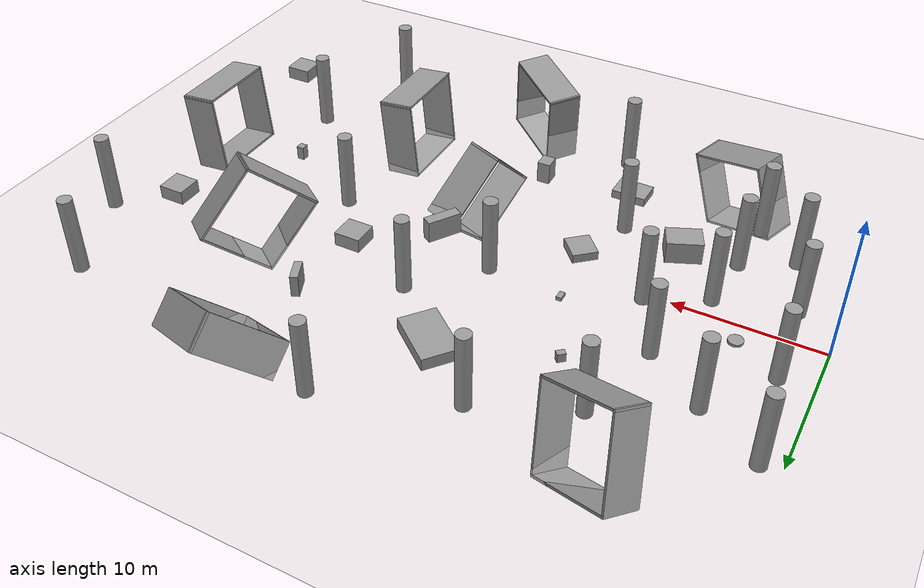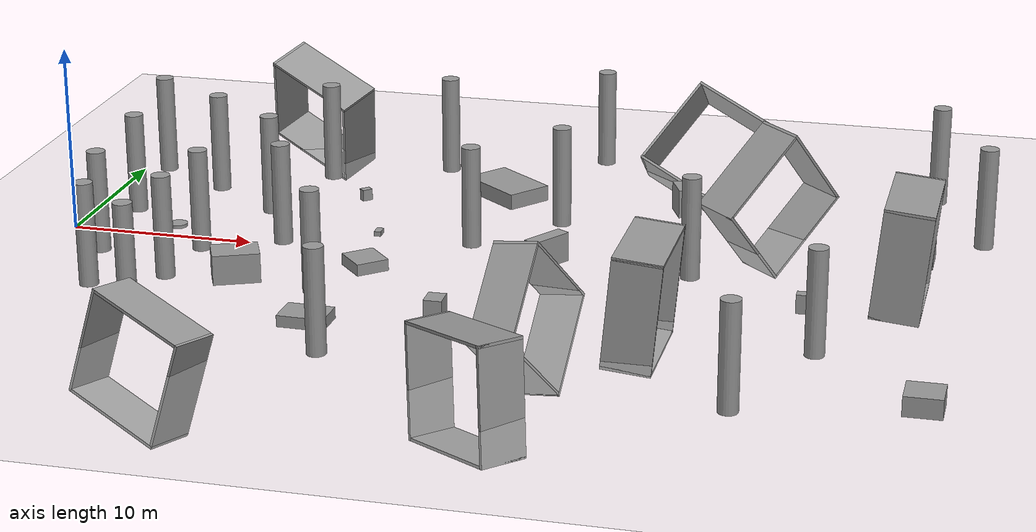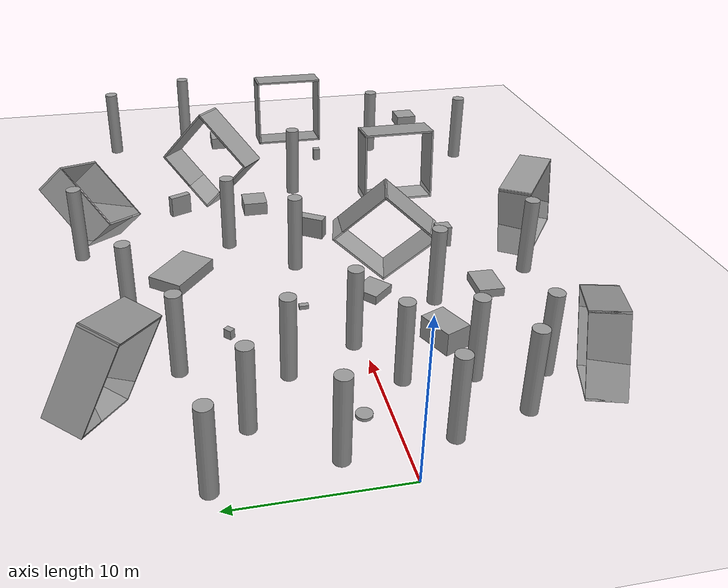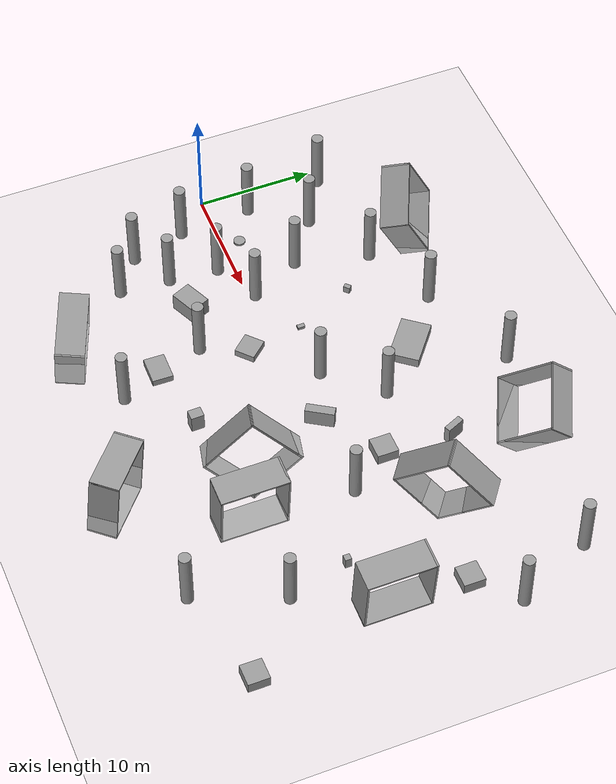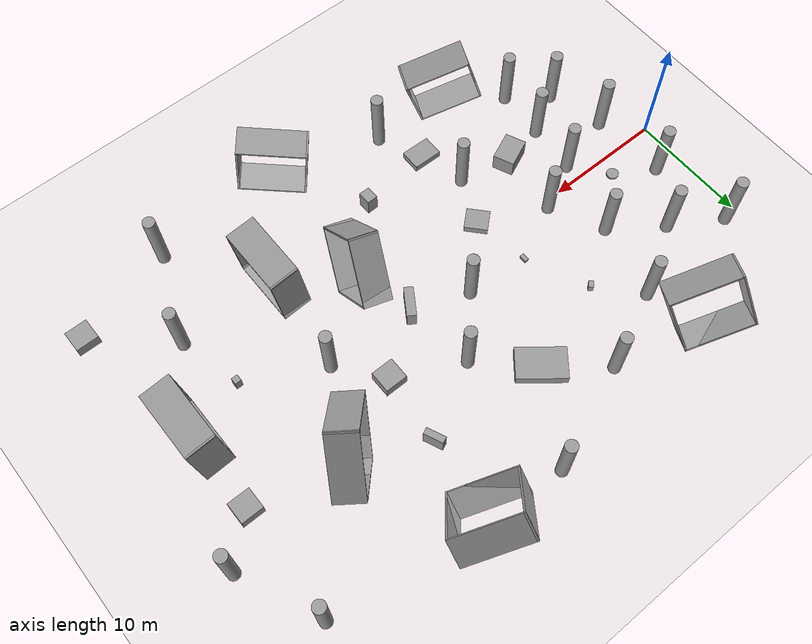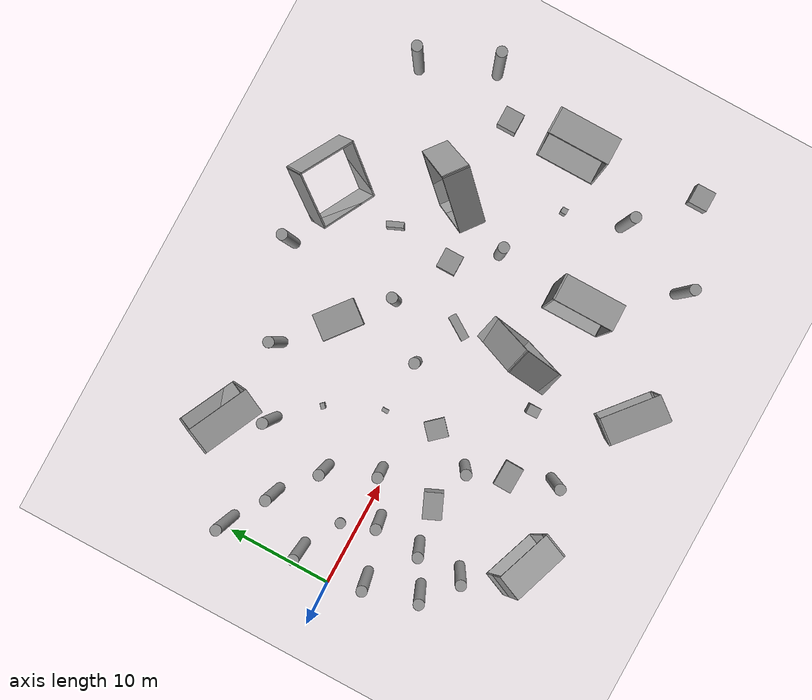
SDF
<sdf version="1.6">
 <world name="default">
  <light name="sun" type="directional">
   <pose>0 0 10 0 -0 0</pose>
   <diffuse>0.8 0.8 0.8 1</diffuse>
   <specular>0.2 0.2 0.2 1</specular>
   <attenuation>
    <range>1000</range>
    <constant>0.9</constant>
    <linear>0.01</linear>
    <quadratic>0.001</quadratic>
   </attenuation>
   <direction>-0.5 0.1 -0.9</direction>
  </light>
  <model name="ground_plane">
   <static>1</static>
   <link name="link">
    <collision name="collision">
     <geometry><plane><normal>0 0 1</normal><size>100 100</size></plane></geometry>
     <surface><friction><ode><mu>100</mu><mu2>50</mu2></ode></friction></surface>
    </collision>
    <visual name="visual">
     <cast_shadows>0</cast_shadows>
     <geometry><plane><normal>0 0 1</normal><size>100 100</size></plane></geometry>
     <material>
      <script><uri>file://media/materials/scripts/gazebo.material</uri><name>Gazebo/Grey</name></script>
     </material>
    </visual>
   </link>
  </model>
  <gravity>0 0 -9.8</gravity>
  <magnetic_field>6e-06 2.3e-05 -4.2e-05</magnetic_field>
  <atmosphere type="adiabatic"/>
  <physics name="default_physics" default="0" type="ode">
   <max_step_size>0.001</max_step_size>
   <real_time_factor>1</real_time_factor>
   <real_time_update_rate>1000</real_time_update_rate>
  </physics>
  <scene><ambient>0.4 0.4 0.4 1</ambient><background>0.7 0.7 0.7 1</background><shadows>1</shadows></scene>
  <audio><device>default</device></audio>
  <spherical_coordinates>
   <surface_model>EARTH_WGS84</surface_model>
   <latitude_deg>0</latitude_deg>
   <longitude_deg>0</longitude_deg>
   <elevation>0</elevation>
   <heading_deg>0</heading_deg>
  </spherical_coordinates>
  <model name="unit_cylinder">
   <pose>5.3177 1.52841 0.090816 0 -0 0.001729</pose>
   <link name="link">
    <inertial>
     <mass>1</mass>
     <inertia><ixx>0.145833</ixx><ixy>0</ixy><ixz>0</ixz><iyy>0.145833</iyy><iyz>0</iyz><izz>0.125</izz></inertia>
    </inertial>
    <collision name="collision">
     <geometry><cylinder><radius>0.5</radius><length>0.18165</length></cylinder></geometry>
    </collision>
    <visual name="visual">
     <geometry><cylinder><radius>0.5</radius><length>0.18165</length></cylinder></geometry>
     <material>
      <script><name>Gazebo/Grey</name><uri>file://media/materials/scripts/gazebo.material</uri></script>
     </material>
    </visual>
   </link>
  </model>
  <model name="unit_cylinder_clone">
   <pose>2.682 -2.80486 2.75253 0 -0 0.001928</pose>
   <link name="link">
    <inertial>
     <mass>1</mass>
     <inertia><ixx>0.145833</ixx><ixy>0</ixy><ixz>0</ixz><iyy>0.145833</iyy><iyz>0</iyz><izz>0.125</izz></inertia>
    </inertial>
    <collision name="collision">
     <geometry><cylinder><radius>0.5</radius><length>5.50507</length></cylinder></geometry>
    </collision>
    <visual name="visual">
     <geometry><cylinder><radius>0.5</radius><length>5.50507</length></cylinder></geometry>
     <material>
      <script><name>Gazebo/Grey</name><uri>file://media/materials/scripts/gazebo.material</uri></script>
     </material>
    </visual>
   </link>
  </model>
  <model name="unit_cylinder_clone_0">
   <pose>2.2289 3.50843 2.75253 0 -0 0.001954</pose>
   <link name="link">
    <inertial>
     <mass>1</mass>
     <inertia><ixx>0.145833</ixx><ixy>0</ixy><ixz>0</ixz><iyy>0.145833</iyy><iyz>0</iyz><izz>0.125</izz></inertia>
    </inertial>
    <collision name="collision">
     <geometry><cylinder><radius>0.5</radius><length>5.50507</length></cylinder></geometry>
    </collision>
    <visual name="visual">
     <geometry><cylinder><radius>0.5</radius><length>5.50507</length></cylinder></geometry>
     <material>
      <script><name>Gazebo/Grey</name><uri>file://media/materials/scripts/gazebo.material</uri></script>
     </material>
    </visual>
   </link>
  </model>
  <model name="unit_cylinder_clone_1">
   <pose>7.38604 -5.59568 2.75253 0 -0 0.001783</pose>
   <link name="link">
    <inertial>
     <mass>1</mass>
     <inertia><ixx>0.145833</ixx><ixy>0</ixy><ixz>0</ixz><iyy>0.145833</iyy><iyz>0</iyz><izz>0.125</izz></inertia>
    </inertial>
    <collision name="collision">
     <geometry><cylinder><radius>0.5</radius><length>5.50507</length></cylinder></geometry>
    </collision>
    <visual name="visual">
     <geometry><cylinder><radius>0.5</radius><length>5.50507</length></cylinder></geometry>
     <material>
      <script><name>Gazebo/Grey</name><uri>file://media/materials/scripts/gazebo.material</uri></script>
     </material>
    </visual>
   </link>
  </model>
  <model name="unit_cylinder_clone_2">
   <pose>9.49523 5.00015 2.75253 0 -0 0.001938</pose>
   <link name="link">
    <inertial>
     <mass>1</mass>
     <inertia><ixx>0.145833</ixx><ixy>0</ixy><ixz>0</ixz><iyy>0.145833</iyy><iyz>0</iyz><izz>0.125</izz></inertia>
    </inertial>
    <collision name="collision">
     <geometry><cylinder><radius>0.5</radius><length>5.50507</length></cylinder></geometry>
    </collision>
    <visual name="visual">
     <geometry><cylinder><radius>0.5</radius><length>5.50507</length></cylinder></geometry>
     <material>
      <script><name>Gazebo/Grey</name><uri>file://media/materials/scripts/gazebo.material</uri></script>
     </material>
    </visual>
   </link>
  </model>
  <model name="unit_cylinder_clone_3">
   <pose>7.77998 -1.3796 2.75253 0 -0 0.002173</pose>
   <link name="link">
    <inertial>
     <mass>1</mass>
     <inertia><ixx>0.145833</ixx><ixy>0</ixy><ixz>0</ixz><iyy>0.145833</iyy><iyz>0</iyz><izz>0.125</izz></inertia>
    </inertial>
    <collision name="collision">
     <geometry><cylinder><radius>0.5</radius><length>5.50507</length></cylinder></geometry>
    </collision>
    <visual name="visual">
     <geometry><cylinder><radius>0.5</radius><length>5.50507</length></cylinder></geometry>
     <material>
      <script><name>Gazebo/Grey</name><uri>file://media/materials/scripts/gazebo.material</uri></script>
     </material>
    </visual>
   </link>
  </model>
  <model name="unit_cylinder_clone_4">
   <pose>3.9885 -7.5392 2.75253 0 -0 0.002246</pose>
   <link name="link">
    <inertial>
     <mass>1</mass>
     <inertia><ixx>0.145833</ixx><ixy>0</ixy><ixz>0</ixz><iyy>0.145833</iyy><iyz>0</iyz><izz>0.125</izz></inertia>
    </inertial>
    <collision name="collision">
     <geometry><cylinder><radius>0.5</radius><length>5.50507</length></cylinder></geometry>
    </collision>
    <visual name="visual">
     <geometry><cylinder><radius>0.5</radius><length>5.50507</length></cylinder></geometry>
     <material>
      <script><name>Gazebo/Grey</name><uri>file://media/materials/scripts/gazebo.material</uri></script>
     </material>
    </visual>
   </link>
  </model>
  <model name="unit_cylinder_clone_5">
   <pose>5.48344 7.91906 2.75253 0 -0 0.001767</pose>
   <link name="link">
    <inertial>
     <mass>1</mass>
     <inertia><ixx>0.145833</ixx><ixy>0</ixy><ixz>0</ixz><iyy>0.145833</iyy><iyz>0</iyz><izz>0.125</izz></inertia>
    </inertial>
    <collision name="collision">
     <geometry><cylinder><radius>0.5</radius><length>5.50507</length></cylinder></geometry>
    </collision>
    <visual name="visual">
     <geometry><cylinder><radius>0.5</radius><length>5.50507</length></cylinder></geometry>
     <material>
      <script><name>Gazebo/Grey</name><uri>file://media/materials/scripts/gazebo.material</uri></script>
     </material>
    </visual>
   </link>
  </model>
  <model name="unit_cylinder_clone_6">
   <pose>7.07562 -9.88009 2.75253 0 -0 0.001971</pose>
   <link name="link">
    <inertial>
     <mass>1</mass>
     <inertia><ixx>0.145833</ixx><ixy>0</ixy><ixz>0</ixz><iyy>0.145833</iyy><iyz>0</iyz><izz>0.125</izz></inertia>
    </inertial>
    <collision name="collision">
     <geometry><cylinder><radius>0.5</radius><length>5.50507</length></cylinder></geometry>
    </collision>
    <visual name="visual">
     <geometry><cylinder><radius>0.5</radius><length>5.50507</length></cylinder></geometry>
     <material>
      <script><name>Gazebo/Grey</name><uri>file://media/materials/scripts/gazebo.material</uri></script>
     </material>
    </visual>
   </link>
  </model>
  <model name="unit_cylinder_clone_7">
   <pose>11.6656 0.575117 2.75253 0 -0 0.001925</pose>
   <link name="link">
    <inertial>
     <mass>1</mass>
     <inertia><ixx>0.145833</ixx><ixy>0</ixy><ixz>0</ixz><iyy>0.145833</iyy><iyz>0</iyz><izz>0.125</izz></inertia>
    </inertial>
    <collision name="collision">
     <geometry><cylinder><radius>0.5</radius><length>5.50507</length></cylinder></geometry>
    </collision>
    <visual name="visual">
     <geometry><cylinder><radius>0.5</radius><length>5.50507</length></cylinder></geometry>
     <material>
      <script><name>Gazebo/Grey</name><uri>file://media/materials/scripts/gazebo.material</uri></script>
     </material>
    </visual>
   </link>
  </model>
  <model name="unit_cylinder_clone_8">
   <pose>11.0404 11.2507 2.75253 0 -0 0.001856</pose>
   <link name="link">
    <inertial>
     <mass>1</mass>
     <inertia><ixx>0.145833</ixx><ixy>0</ixy><ixz>0</ixz><iyy>0.145833</iyy><iyz>0</iyz><izz>0.125</izz></inertia>
    </inertial>
    <collision name="collision">
     <geometry><cylinder><radius>0.5</radius><length>5.50507</length></cylinder></geometry>
    </collision>
    <visual name="visual">
     <geometry><cylinder><radius>0.5</radius><length>5.50507</length></cylinder></geometry>
     <material>
      <script><name>Gazebo/Grey</name><uri>file://media/materials/scripts/gazebo.material</uri></script>
     </material>
    </visual>
   </link>
  </model>
  <model name="unit_cylinder_clone_9">
   <pose>1.32565 10.3756 2.75253 0 -0 0.002036</pose>
   <link name="link">
    <inertial>
     <mass>1</mass>
     <inertia><ixx>0.145833</ixx><ixy>0</ixy><ixz>0</ixz><iyy>0.145833</iyy><iyz>0</iyz><izz>0.125</izz></inertia>
    </inertial>
    <collision name="collision">
     <geometry><cylinder><radius>0.5</radius><length>5.50507</length></cylinder></geometry>
    </collision>
    <visual name="visual">
     <geometry><cylinder><radius>0.5</radius><length>5.50507</length></cylinder></geometry>
     <material>
      <script><name>Gazebo/Grey</name><uri>file://media/materials/scripts/gazebo.material</uri></script>
     </material>
    </visual>
   </link>
  </model>
  <model name="unit_cylinder_clone_12">
   <pose>15.4144 -5.85672 2.75253 0 -0 0.002175</pose>
   <link name="link">
    <inertial>
     <mass>1</mass>
     <inertia><ixx>0.145833</ixx><ixy>0</ixy><ixz>0</ixz><iyy>0.145833</iyy><iyz>0</iyz><izz>0.125</izz></inertia>
    </inertial>
    <collision name="collision">
     <geometry><cylinder><radius>0.5</radius><length>5.50507</length></cylinder></geometry>
    </collision>
    <visual name="visual">
     <geometry><cylinder><radius>0.5</radius><length>5.50507</length></cylinder></geometry>
     <material>
      <script><name>Gazebo/Grey</name><uri>file://media/materials/scripts/gazebo.material</uri></script>
     </material>
    </visual>
   </link>
  </model>
  <model name="unit_box">
   <pose>13.9889 7.9962 0.317164 0 -0 0.738864</pose>
   <link name="link">
    <inertial>
     <mass>1</mass>
     <inertia>
      <ixx>0.166667</ixx>
      <ixy>0</ixy>
      <ixz>0</ixz>
      <iyy>0.166667</iyy>
      <iyz>0</iyz>
      <izz>0.166667</izz>
     </inertia>
    </inertial>
    <collision name="collision">
     <geometry><box><size>0.564982 0.408969 0.634329</size></box></geometry>
    </collision>
    <visual name="visual">
     <geometry><box><size>0.564982 0.408969 0.634329</size></box></geometry>
     <material>
      <script><name>Gazebo/Grey</name><uri>file://media/materials/scripts/gazebo.material</uri></script>
     </material>
    </visual>
   </link>
  </model>
  <model name="unit_box_clone">
   <pose>11.0027 -5 0.788235 0 0 -1.15764</pose>
   <link name="link">
    <inertial>
     <mass>1</mass>
     <inertia>
      <ixx>0.166667</ixx>
      <ixy>0</ixy>
      <ixz>0</ixz>
      <iyy>0.166667</iyy>
      <iyz>0</iyz>
      <izz>0.166667</izz>
     </inertia>
    </inertial>
    <collision name="collision"><geometry><box><size>1.76997 2.44518 1.57647</size></box></geometry></collision>
    <visual name="visual">
     <geometry><box><size>1.76997 2.44518 1.57647</size></box></geometry>
     <material>
      <script><name>Gazebo/Grey</name><uri>file://media/materials/scripts/gazebo.material</uri></script>
     </material>
    </visual>
   </link>
  </model>
  <model name="unit_box_clone_0">
   <pose>17.0316 -2.04216 0.311636 0 -0 0.732674</pose>
   <link name="link">
    <inertial>
     <mass>1</mass>
     <inertia>
      <ixx>0.166667</ixx>
      <ixy>0</ixy>
      <ixz>0</ixz>
      <iyy>0.166667</iyy>
      <iyz>0</iyz>
      <izz>0.166667</izz>
     </inertia>
    </inertial>
    <collision name="collision"><geometry><box><size>1.76997 1.92154 0.623272</size></box></geometry></collision>
    <visual name="visual">
     <geometry><box><size>1.76997 1.92154 0.623272</size></box></geometry>
     <material>
      <script><name>Gazebo/Grey</name><uri>file://media/materials/scripts/gazebo.material</uri></script>
     </material>
    </visual>
   </link>
  </model>
  <model name="unit_box_clone_1">
   <pose>16.398 -9.83684 0.300237 0 1.4e-05 1.55078</pose>
   <link name="link">
    <inertial>
     <mass>1</mass>
     <inertia>
      <ixx>0.166667</ixx>
      <ixy>0</ixy>
      <ixz>0</ixz>
      <iyy>0.166667</iyy>
      <iyz>0</iyz>
      <izz>0.166667</izz>
     </inertia>
    </inertial>
    <collision name="collision"><geometry><box><size>1.76997 2.44518 0.600499</size></box></geometry></collision>
    <visual name="visual">
     <geometry><box><size>1.76997 2.44518 0.600499</size></box></geometry>
     <material>
      <script><name>Gazebo/Grey</name><uri>file://media/materials/scripts/gazebo.material</uri></script>
     </material>
    </visual>
   </link>
  </model>
  <model name="unit_box_clone_0_clone">
   <pose>21.5279 10.4923 0.43037 3.14159 -1.57079 2.4667</pose>
   <link name="link">
    <inertial>
     <mass>1</mass>
     <inertia>
      <ixx>0.166667</ixx>
      <ixy>0</ixy>
      <ixz>0</ixz>
      <iyy>0.166667</iyy>
      <iyz>0</iyz>
      <izz>0.166667</izz>
     </inertia>
    </inertial>
    <collision name="collision"><geometry><box><size>0.860775 2.57296 3.98743</size></box></geometry></collision>
    <visual name="visual">
     <geometry><box><size>0.860775 2.57296 3.98743</size></box></geometry>
     <material>
      <script><name>Gazebo/Grey</name><uri>file://media/materials/scripts/gazebo.material</uri></script>
     </material>
    </visual>
   </link>
  </model>
  <model name="unit_box_0">
   <pose>16.3006 2.8364 0.132103 -0 -7e-06 -0.000455</pose>
   <link name="link">
    <inertial>
     <mass>1</mass>
     <inertia>
      <ixx>0.166667</ixx>
      <ixy>0</ixy>
      <ixz>0</ixz>
      <iyy>0.166667</iyy>
      <iyz>0</iyz>
      <izz>0.166667</izz>
     </inertia>
    </inertial>
    <collision name="collision">
     <geometry><box><size>0.372249 0.631413 0.264209</size></box></geometry>
    </collision>
    <visual name="visual">
     <geometry><box><size>0.372249 0.631413 0.264209</size></box></geometry>
     <material>
      <script><name>Gazebo/Grey</name><uri>file://media/materials/scripts/gazebo.material</uri></script>
     </material>
    </visual>
   </link>
  </model>
  <model name="unit_box_clone_clone">
   <pose>26.0956 0.593964 0.788231 4e-06 -0 -0.569843</pose>
   <link name="link">
    <inertial>
     <mass>1</mass>
     <inertia>
      <ixx>0.166667</ixx>
      <ixy>0</ixy>
      <ixz>0</ixz>
      <iyy>0.166667</iyy>
      <iyz>0</iyz>
      <izz>0.166667</izz>
     </inertia>
    </inertial>
    <collision name="collision"><geometry><box><size>0.770315 2.44518 1.57647</size></box></geometry></collision>
    <visual name="visual">
     <geometry><box><size>0.770315 2.44518 1.57647</size></box></geometry>
     <material>
      <script><name>Gazebo/Grey</name><uri>file://media/materials/scripts/gazebo.material</uri></script>
     </material>
    </visual>
   </link>
  </model>
  <model name="unit_box_clone_clone_0">
   <pose>22.7246 -8.85656 0.788231 6e-06 -1e-06 0.019044</pose>
   <link name="link">
    <inertial>
     <mass>1</mass>
     <inertia>
      <ixx>0.166667</ixx>
      <ixy>0</ixy>
      <ixz>0</ixz>
      <iyy>0.166667</iyy>
      <iyz>0</iyz>
      <izz>0.166667</izz>
     </inertia>
    </inertial>
    <collision name="collision"><geometry><box><size>0.926366 1.10204 1.57647</size></box></geometry></collision>
    <visual name="visual">
     <geometry><box><size>0.926366 1.10204 1.57647</size></box></geometry>
     <material>
      <script><name>Gazebo/Grey</name><uri>file://media/materials/scripts/gazebo.material</uri></script>
     </material>
    </visual>
   </link>
  </model>
  <model name="unit_box_clone_clone_1">
   <pose>31.4554 9.98516 0.788235 0 -0 -2.73194</pose>
   <link name="link">
    <inertial>
     <mass>1</mass>
     <inertia>
      <ixx>0.166667</ixx>
      <ixy>0</ixy>
      <ixz>0</ixz>
      <iyy>0.166667</iyy>
      <iyz>0</iyz>
      <izz>0.166667</izz>
     </inertia>
    </inertial>
    <collision name="collision"><geometry><box><size>0.539862 1.60938 1.57647</size></box></geometry></collision>
    <visual name="visual">
     <geometry><box><size>0.539862 1.60938 1.57647</size></box></geometry>
     <material>
      <script><name>Gazebo/Grey</name><uri>file://media/materials/scripts/gazebo.material</uri></script>
     </material>
    </visual>
   </link>
  </model>
  <model name="unit_cylinder_clone_7_clone_0">
   <pose>25.5042 6.72841 2.75253 0 -0 0.001921</pose>
   <link name="link">
    <inertial>
     <mass>1</mass>
     <inertia><ixx>0.145833</ixx><ixy>0</ixy><ixz>0</ixz><iyy>0.145833</iyy><iyz>0</iyz><izz>0.125</izz></inertia>
    </inertial>
    <collision name="collision">
     <geometry><cylinder><radius>0.5</radius><length>5.50507</length></cylinder></geometry>
    </collision>
    <visual name="visual">
     <geometry><cylinder><radius>0.5</radius><length>5.50507</length></cylinder></geometry>
     <material>
      <script><name>Gazebo/Grey</name><uri>file://media/materials/scripts/gazebo.material</uri></script>
     </material>
    </visual>
   </link>
  </model>
  <model name="unit_cylinder_clone_7_clone_1">
   <pose>21.5657 2.44797 2.75253 0 -0 0.001806</pose>
   <link name="link">
    <inertial>
     <mass>1</mass>
     <inertia><ixx>0.145833</ixx><ixy>0</ixy><ixz>0</ixz><iyy>0.145833</iyy><iyz>0</iyz><izz>0.125</izz></inertia>
    </inertial>
    <collision name="collision">
     <geometry><cylinder><radius>0.5</radius><length>5.50507</length></cylinder></geometry>
    </collision>
    <visual name="visual">
     <geometry><cylinder><radius>0.5</radius><length>5.50507</length></cylinder></geometry>
     <material>
      <script><name>Gazebo/Grey</name><uri>file://media/materials/scripts/gazebo.material</uri></script>
     </material>
    </visual>
   </link>
  </model>
  <model name="unit_cylinder_clone_7_clone_2">
   <pose>17.2812 14.0464 2.75253 0 -0 0.001804</pose>
   <link name="link">
    <inertial>
     <mass>1</mass>
     <inertia><ixx>0.145833</ixx><ixy>0</ixy><ixz>0</ixz><iyy>0.145833</iyy><iyz>0</iyz><izz>0.125</izz></inertia>
    </inertial>
    <collision name="collision">
     <geometry><cylinder><radius>0.5</radius><length>5.50507</length></cylinder></geometry>
    </collision>
    <visual name="visual">
     <geometry><cylinder><radius>0.5</radius><length>5.50507</length></cylinder></geometry>
     <material>
      <script><name>Gazebo/Grey</name><uri>file://media/materials/scripts/gazebo.material</uri></script>
     </material>
    </visual>
   </link>
  </model>
  <model name="unit_cylinder_clone_7_clone_3">
   <pose>18.1074 -13.3673 2.75253 0 -0 0.001857</pose>
   <link name="link">
    <inertial>
     <mass>1</mass>
     <inertia><ixx>0.145833</ixx><ixy>0</ixy><ixz>0</ixz><iyy>0.145833</iyy><iyz>0</iyz><izz>0.125</izz></inertia>
    </inertial>
    <collision name="collision">
     <geometry><cylinder><radius>0.5</radius><length>5.50507</length></cylinder></geometry>
    </collision>
    <visual name="visual">
     <geometry><cylinder><radius>0.5</radius><length>5.50507</length></cylinder></geometry>
     <material>
      <script><name>Gazebo/Grey</name><uri>file://media/materials/scripts/gazebo.material</uri></script>
     </material>
    </visual>
   </link>
  </model>
  <model name="vRoom_clone_3_clone_clone_9">
   <link name="Wall_0">
    <pose>-2.8 -0 -1e-06 -0 -0 -1.5708</pose>
    <velocity_decay><linear>0</linear><angular>0</angular></velocity_decay>
    <visual name="Wall_0_Visual">
     <pose>0 0 1.25 0 -0 0</pose>
     <geometry><box><size>5.75 0.15 2.5</size></box></geometry>
     <material>
      <script><uri>file://media/materials/scripts/gazebo.material</uri><name>Gazebo/Grey</name></script>
      <ambient>1 1 1 1</ambient>
     </material>
    </visual>
    <collision name="Wall_0_Collision">
     <pose>0 0 1.25 0 -0 0</pose>
     <geometry><box><size>5.75 0.15 2.5</size></box></geometry>
     <surface>
      <friction>
       <ode><mu>1</mu><mu2>1</mu2><fdir1>0 0 0</fdir1><slip1>0</slip1><slip2>0</slip2></ode>
       <torsional>
        <coefficient>1</coefficient>
        <patch_radius>0</patch_radius>
        <surface_radius>0</surface_radius>
        <use_patch_radius>1</use_patch_radius>
        <ode><slip>0</slip></ode>
       </torsional>
      </friction>
      <bounce><restitution_coefficient>0</restitution_coefficient><threshold>1e+06</threshold></bounce>
      <contact>
       <collide_without_contact>0</collide_without_contact>
       <collide_without_contact_bitmask>1</collide_without_contact_bitmask>
       <collide_bitmask>1</collide_bitmask>
       <ode>
        <soft_cfm>0</soft_cfm>
        <soft_erp>0.2</soft_erp>
        <kp>1e+13</kp>
        <kd>1</kd>
        <max_vel>0.01</max_vel>
        <min_depth>0</min_depth>
       </ode>
       <bullet>
        <split_impulse>1</split_impulse>
        <split_impulse_penetration_threshold>-0.01</split_impulse_penetration_threshold>
        <soft_cfm>0</soft_cfm>
        <soft_erp>0.2</soft_erp>
        <kp>1e+13</kp>
        <kd>1</kd>
       </bullet>
      </contact>
     </surface>
    </collision>
   </link>
   <link name="Wall_1">
    <pose>2e-06 -2.8 2e-06 0 -0 0</pose>
    <velocity_decay><linear>0</linear><angular>0</angular></velocity_decay>
    <visual name="Wall_1_Visual">
     <pose>0 0 1.25 0 -0 0</pose>
     <geometry><box><size>5.75 0.15 2.5</size></box></geometry>
     <material>
      <script><uri>file://media/materials/scripts/gazebo.material</uri><name>Gazebo/Grey</name></script>
      <ambient>1 1 1 1</ambient>
     </material>
    </visual>
    <collision name="Wall_1_Collision">
     <pose>0 0 1.25 0 -0 0</pose>
     <geometry><box><size>5.75 0.15 2.5</size></box></geometry>
     <surface>
      <friction>
       <ode><mu>1</mu><mu2>1</mu2><fdir1>0 0 0</fdir1><slip1>0</slip1><slip2>0</slip2></ode>
       <torsional>
        <coefficient>1</coefficient>
        <patch_radius>0</patch_radius>
        <surface_radius>0</surface_radius>
        <use_patch_radius>1</use_patch_radius>
        <ode><slip>0</slip></ode>
       </torsional>
      </friction>
      <bounce><restitution_coefficient>0</restitution_coefficient><threshold>1e+06</threshold></bounce>
      <contact>
       <collide_without_contact>0</collide_without_contact>
       <collide_without_contact_bitmask>1</collide_without_contact_bitmask>
       <collide_bitmask>1</collide_bitmask>
       <ode>
        <soft_cfm>0</soft_cfm>
        <soft_erp>0.2</soft_erp>
        <kp>1e+13</kp>
        <kd>1</kd>
        <max_vel>0.01</max_vel>
        <min_depth>0</min_depth>
       </ode>
       <bullet>
        <split_impulse>1</split_impulse>
        <split_impulse_penetration_threshold>-0.01</split_impulse_penetration_threshold>
        <soft_cfm>0</soft_cfm>
        <soft_erp>0.2</soft_erp>
        <kp>1e+13</kp>
        <kd>1</kd>
       </bullet>
      </contact>
     </surface>
    </collision>
   </link>
   <link name="Wall_2">
    <pose>2.8 0 1e-06 0 -0 1.5708</pose>
    <velocity_decay><linear>0</linear><angular>0</angular></velocity_decay>
    <visual name="Wall_2_Visual">
     <pose>0 0 1.25 0 -0 0</pose>
     <geometry><box><size>5.75 0.15 2.5</size></box></geometry>
     <material>
      <script><uri>file://media/materials/scripts/gazebo.material</uri><name>Gazebo/Grey</name></script>
      <ambient>1 1 1 1</ambient>
     </material>
    </visual>
    <collision name="Wall_2_Collision">
     <pose>0 0 1.25 0 -0 0</pose>
     <geometry><box><size>5.75 0.15 2.5</size></box></geometry>
     <surface>
      <friction>
       <ode><mu>1</mu><mu2>1</mu2><fdir1>0 0 0</fdir1><slip1>0</slip1><slip2>0</slip2></ode>
       <torsional>
        <coefficient>1</coefficient>
        <patch_radius>0</patch_radius>
        <surface_radius>0</surface_radius>
        <use_patch_radius>1</use_patch_radius>
        <ode><slip>0</slip></ode>
       </torsional>
      </friction>
      <bounce><restitution_coefficient>0</restitution_coefficient><threshold>1e+06</threshold></bounce>
      <contact>
       <collide_without_contact>0</collide_without_contact>
       <collide_without_contact_bitmask>1</collide_without_contact_bitmask>
       <collide_bitmask>1</collide_bitmask>
       <ode>
        <soft_cfm>0</soft_cfm>
        <soft_erp>0.2</soft_erp>
        <kp>1e+13</kp>
        <kd>1</kd>
        <max_vel>0.01</max_vel>
        <min_depth>0</min_depth>
       </ode>
       <bullet>
        <split_impulse>1</split_impulse>
        <split_impulse_penetration_threshold>-0.01</split_impulse_penetration_threshold>
        <soft_cfm>0</soft_cfm>
        <soft_erp>0.2</soft_erp>
        <kp>1e+13</kp>
        <kd>1</kd>
       </bullet>
      </contact>
     </surface>
    </collision>
   </link>
   <link name="Wall_3">
    <pose>-2e-06 2.8 -2e-06 0 -0 3.14159</pose>
    <velocity_decay><linear>0</linear><angular>0</angular></velocity_decay>
    <visual name="Wall_3_Visual">
     <pose>0 0 1.25 0 -0 0</pose>
     <geometry><box><size>5.75 0.15 2.5</size></box></geometry>
     <material>
      <script><uri>file://media/materials/scripts/gazebo.material</uri><name>Gazebo/Grey</name></script>
      <ambient>1 1 1 1</ambient>
     </material>
    </visual>
    <collision name="Wall_3_Collision">
     <pose>0 0 1.25 0 -0 0</pose>
     <geometry><box><size>5.75 0.15 2.5</size></box></geometry>
     <surface>
      <friction>
       <ode><mu>1</mu><mu2>1</mu2><fdir1>0 0 0</fdir1><slip1>0</slip1><slip2>0</slip2></ode>
       <torsional>
        <coefficient>1</coefficient>
        <patch_radius>0</patch_radius>
        <surface_radius>0</surface_radius>
        <use_patch_radius>1</use_patch_radius>
        <ode><slip>0</slip></ode>
       </torsional>
      </friction>
      <bounce><restitution_coefficient>0</restitution_coefficient><threshold>1e+06</threshold></bounce>
      <contact>
       <collide_without_contact>0</collide_without_contact>
       <collide_without_contact_bitmask>1</collide_without_contact_bitmask>
       <collide_bitmask>1</collide_bitmask>
       <ode>
        <soft_cfm>0</soft_cfm>
        <soft_erp>0.2</soft_erp>
        <kp>1e+13</kp>
        <kd>1</kd>
        <max_vel>0.01</max_vel>
        <min_depth>0</min_depth>
       </ode>
       <bullet>
        <split_impulse>1</split_impulse>
        <split_impulse_penetration_threshold>-0.01</split_impulse_penetration_threshold>
        <soft_cfm>0</soft_cfm>
        <soft_erp>0.2</soft_erp>
        <kp>1e+13</kp>
        <kd>1</kd>
       </bullet>
      </contact>
     </surface>
    </collision>
   </link>
   <static>1</static>
   <pose>34.1246 -8.07118 2.16038 4e-06 -1.47998 -7e-06</pose>
  </model>
  <model name="vRoom_clone_3_clone_clone_9_clone">
   <link name="Wall_0">
    <pose>-2.8 -0 -1e-06 -0 -0 -1.5708</pose>
    <velocity_decay><linear>0</linear><angular>0</angular></velocity_decay>
    <visual name="Wall_0_Visual">
     <pose>0 0 1.25 0 -0 0</pose>
     <geometry><box><size>5.75 0.15 2.5</size></box></geometry>
     <material>
      <script><uri>file://media/materials/scripts/gazebo.material</uri><name>Gazebo/Grey</name></script>
      <ambient>1 1 1 1</ambient>
     </material>
    </visual>
    <collision name="Wall_0_Collision">
     <pose>0 0 1.25 0 -0 0</pose>
     <geometry><box><size>5.75 0.15 2.5</size></box></geometry>
     <surface>
      <friction>
       <ode><mu>1</mu><mu2>1</mu2><fdir1>0 0 0</fdir1><slip1>0</slip1><slip2>0</slip2></ode>
       <torsional>
        <coefficient>1</coefficient>
        <patch_radius>0</patch_radius>
        <surface_radius>0</surface_radius>
        <use_patch_radius>1</use_patch_radius>
        <ode><slip>0</slip></ode>
       </torsional>
      </friction>
      <bounce><restitution_coefficient>0</restitution_coefficient><threshold>1e+06</threshold></bounce>
      <contact>
       <collide_without_contact>0</collide_without_contact>
       <collide_without_contact_bitmask>1</collide_without_contact_bitmask>
       <collide_bitmask>1</collide_bitmask>
       <ode>
        <soft_cfm>0</soft_cfm>
        <soft_erp>0.2</soft_erp>
        <kp>1e+13</kp>
        <kd>1</kd>
        <max_vel>0.01</max_vel>
        <min_depth>0</min_depth>
       </ode>
       <bullet>
        <split_impulse>1</split_impulse>
        <split_impulse_penetration_threshold>-0.01</split_impulse_penetration_threshold>
        <soft_cfm>0</soft_cfm>
        <soft_erp>0.2</soft_erp>
        <kp>1e+13</kp>
        <kd>1</kd>
       </bullet>
      </contact>
     </surface>
    </collision>
   </link>
   <link name="Wall_1">
    <pose>2e-06 -2.8 2e-06 0 -0 0</pose>
    <velocity_decay><linear>0</linear><angular>0</angular></velocity_decay>
    <visual name="Wall_1_Visual">
     <pose>0 0 1.25 0 -0 0</pose>
     <geometry><box><size>5.75 0.15 2.5</size></box></geometry>
     <material>
      <script><uri>file://media/materials/scripts/gazebo.material</uri><name>Gazebo/Grey</name></script>
      <ambient>1 1 1 1</ambient>
     </material>
    </visual>
    <collision name="Wall_1_Collision">
     <pose>0 0 1.25 0 -0 0</pose>
     <geometry><box><size>5.75 0.15 2.5</size></box></geometry>
     <surface>
      <friction>
       <ode><mu>1</mu><mu2>1</mu2><fdir1>0 0 0</fdir1><slip1>0</slip1><slip2>0</slip2></ode>
       <torsional>
        <coefficient>1</coefficient>
        <patch_radius>0</patch_radius>
        <surface_radius>0</surface_radius>
        <use_patch_radius>1</use_patch_radius>
        <ode><slip>0</slip></ode>
       </torsional>
      </friction>
      <bounce><restitution_coefficient>0</restitution_coefficient><threshold>1e+06</threshold></bounce>
      <contact>
       <collide_without_contact>0</collide_without_contact>
       <collide_without_contact_bitmask>1</collide_without_contact_bitmask>
       <collide_bitmask>1</collide_bitmask>
       <ode>
        <soft_cfm>0</soft_cfm>
        <soft_erp>0.2</soft_erp>
        <kp>1e+13</kp>
        <kd>1</kd>
        <max_vel>0.01</max_vel>
        <min_depth>0</min_depth>
       </ode>
       <bullet>
        <split_impulse>1</split_impulse>
        <split_impulse_penetration_threshold>-0.01</split_impulse_penetration_threshold>
        <soft_cfm>0</soft_cfm>
        <soft_erp>0.2</soft_erp>
        <kp>1e+13</kp>
        <kd>1</kd>
       </bullet>
      </contact>
     </surface>
    </collision>
   </link>
   <link name="Wall_2">
    <pose>2.8 0 1e-06 0 -0 1.5708</pose>
    <velocity_decay><linear>0</linear><angular>0</angular></velocity_decay>
    <visual name="Wall_2_Visual">
     <pose>0 0 1.25 0 -0 0</pose>
     <geometry><box><size>5.75 0.15 2.5</size></box></geometry>
     <material>
      <script><uri>file://media/materials/scripts/gazebo.material</uri><name>Gazebo/Grey</name></script>
      <ambient>1 1 1 1</ambient>
     </material>
    </visual>
    <collision name="Wall_2_Collision">
     <pose>0 0 1.25 0 -0 0</pose>
     <geometry><box><size>5.75 0.15 2.5</size></box></geometry>
     <surface>
      <friction>
       <ode><mu>1</mu><mu2>1</mu2><fdir1>0 0 0</fdir1><slip1>0</slip1><slip2>0</slip2></ode>
       <torsional>
        <coefficient>1</coefficient>
        <patch_radius>0</patch_radius>
        <surface_radius>0</surface_radius>
        <use_patch_radius>1</use_patch_radius>
        <ode><slip>0</slip></ode>
       </torsional>
      </friction>
      <bounce><restitution_coefficient>0</restitution_coefficient><threshold>1e+06</threshold></bounce>
      <contact>
       <collide_without_contact>0</collide_without_contact>
       <collide_without_contact_bitmask>1</collide_without_contact_bitmask>
       <collide_bitmask>1</collide_bitmask>
       <ode>
        <soft_cfm>0</soft_cfm>
        <soft_erp>0.2</soft_erp>
        <kp>1e+13</kp>
        <kd>1</kd>
        <max_vel>0.01</max_vel>
        <min_depth>0</min_depth>
       </ode>
       <bullet>
        <split_impulse>1</split_impulse>
        <split_impulse_penetration_threshold>-0.01</split_impulse_penetration_threshold>
        <soft_cfm>0</soft_cfm>
        <soft_erp>0.2</soft_erp>
        <kp>1e+13</kp>
        <kd>1</kd>
       </bullet>
      </contact>
     </surface>
    </collision>
   </link>
   <link name="Wall_3">
    <pose>-2e-06 2.8 -2e-06 0 -0 3.14159</pose>
    <velocity_decay><linear>0</linear><angular>0</angular></velocity_decay>
    <visual name="Wall_3_Visual">
     <pose>0 0 1.25 0 -0 0</pose>
     <geometry><box><size>5.75 0.15 2.5</size></box></geometry>
     <material>
      <script><uri>file://media/materials/scripts/gazebo.material</uri><name>Gazebo/Grey</name></script>
      <ambient>1 1 1 1</ambient>
     </material>
    </visual>
    <collision name="Wall_3_Collision">
     <pose>0 0 1.25 0 -0 0</pose>
     <geometry><box><size>5.75 0.15 2.5</size></box></geometry>
     <surface>
      <friction>
       <ode><mu>1</mu><mu2>1</mu2><fdir1>0 0 0</fdir1><slip1>0</slip1><slip2>0</slip2></ode>
       <torsional>
        <coefficient>1</coefficient>
        <patch_radius>0</patch_radius>
        <surface_radius>0</surface_radius>
        <use_patch_radius>1</use_patch_radius>
        <ode><slip>0</slip></ode>
       </torsional>
      </friction>
      <bounce><restitution_coefficient>0</restitution_coefficient><threshold>1e+06</threshold></bounce>
      <contact>
       <collide_without_contact>0</collide_without_contact>
       <collide_without_contact_bitmask>1</collide_without_contact_bitmask>
       <collide_bitmask>1</collide_bitmask>
       <ode>
        <soft_cfm>0</soft_cfm>
        <soft_erp>0.2</soft_erp>
        <kp>1e+13</kp>
        <kd>1</kd>
        <max_vel>0.01</max_vel>
        <min_depth>0</min_depth>
       </ode>
       <bullet>
        <split_impulse>1</split_impulse>
        <split_impulse_penetration_threshold>-0.01</split_impulse_penetration_threshold>
        <soft_cfm>0</soft_cfm>
        <soft_erp>0.2</soft_erp>
        <kp>1e+13</kp>
        <kd>1</kd>
       </bullet>
      </contact>
     </surface>
    </collision>
   </link>
   <static>1</static>
   <pose>37.7929 6.19167 2.16038 1.45974 -0.860248 -2.1368</pose>
  </model>
  <model name="vRoom_clone_3_clone_clone_9_clone_0">
   <link name="Wall_0">
    <pose>-2.8 -0 -1e-06 -0 -0 -1.5708</pose>
    <velocity_decay><linear>0</linear><angular>0</angular></velocity_decay>
    <visual name="Wall_0_Visual">
     <pose>0 0 1.25 0 -0 0</pose>
     <geometry><box><size>5.75 0.15 2.5</size></box></geometry>
     <material>
      <script><uri>file://media/materials/scripts/gazebo.material</uri><name>Gazebo/Grey</name></script>
      <ambient>1 1 1 1</ambient>
     </material>
    </visual>
    <collision name="Wall_0_Collision">
     <pose>0 0 1.25 0 -0 0</pose>
     <geometry><box><size>5.75 0.15 2.5</size></box></geometry>
     <surface>
      <friction>
       <ode><mu>1</mu><mu2>1</mu2><fdir1>0 0 0</fdir1><slip1>0</slip1><slip2>0</slip2></ode>
       <torsional>
        <coefficient>1</coefficient>
        <patch_radius>0</patch_radius>
        <surface_radius>0</surface_radius>
        <use_patch_radius>1</use_patch_radius>
        <ode><slip>0</slip></ode>
       </torsional>
      </friction>
      <bounce><restitution_coefficient>0</restitution_coefficient><threshold>1e+06</threshold></bounce>
      <contact>
       <collide_without_contact>0</collide_without_contact>
       <collide_without_contact_bitmask>1</collide_without_contact_bitmask>
       <collide_bitmask>1</collide_bitmask>
       <ode>
        <soft_cfm>0</soft_cfm>
        <soft_erp>0.2</soft_erp>
        <kp>1e+13</kp>
        <kd>1</kd>
        <max_vel>0.01</max_vel>
        <min_depth>0</min_depth>
       </ode>
       <bullet>
        <split_impulse>1</split_impulse>
        <split_impulse_penetration_threshold>-0.01</split_impulse_penetration_threshold>
        <soft_cfm>0</soft_cfm>
        <soft_erp>0.2</soft_erp>
        <kp>1e+13</kp>
        <kd>1</kd>
       </bullet>
      </contact>
     </surface>
    </collision>
   </link>
   <link name="Wall_1">
    <pose>2e-06 -2.8 2e-06 0 -0 0</pose>
    <velocity_decay><linear>0</linear><angular>0</angular></velocity_decay>
    <visual name="Wall_1_Visual">
     <pose>0 0 1.25 0 -0 0</pose>
     <geometry><box><size>5.75 0.15 2.5</size></box></geometry>
     <material>
      <script><uri>file://media/materials/scripts/gazebo.material</uri><name>Gazebo/Grey</name></script>
      <ambient>1 1 1 1</ambient>
     </material>
    </visual>
    <collision name="Wall_1_Collision">
     <pose>0 0 1.25 0 -0 0</pose>
     <geometry><box><size>5.75 0.15 2.5</size></box></geometry>
     <surface>
      <friction>
       <ode><mu>1</mu><mu2>1</mu2><fdir1>0 0 0</fdir1><slip1>0</slip1><slip2>0</slip2></ode>
       <torsional>
        <coefficient>1</coefficient>
        <patch_radius>0</patch_radius>
        <surface_radius>0</surface_radius>
        <use_patch_radius>1</use_patch_radius>
        <ode><slip>0</slip></ode>
       </torsional>
      </friction>
      <bounce><restitution_coefficient>0</restitution_coefficient><threshold>1e+06</threshold></bounce>
      <contact>
       <collide_without_contact>0</collide_without_contact>
       <collide_without_contact_bitmask>1</collide_without_contact_bitmask>
       <collide_bitmask>1</collide_bitmask>
       <ode>
        <soft_cfm>0</soft_cfm>
        <soft_erp>0.2</soft_erp>
        <kp>1e+13</kp>
        <kd>1</kd>
        <max_vel>0.01</max_vel>
        <min_depth>0</min_depth>
       </ode>
       <bullet>
        <split_impulse>1</split_impulse>
        <split_impulse_penetration_threshold>-0.01</split_impulse_penetration_threshold>
        <soft_cfm>0</soft_cfm>
        <soft_erp>0.2</soft_erp>
        <kp>1e+13</kp>
        <kd>1</kd>
       </bullet>
      </contact>
     </surface>
    </collision>
   </link>
   <link name="Wall_2">
    <pose>2.8 0 1e-06 0 -0 1.5708</pose>
    <velocity_decay><linear>0</linear><angular>0</angular></velocity_decay>
    <visual name="Wall_2_Visual">
     <pose>0 0 1.25 0 -0 0</pose>
     <geometry><box><size>5.75 0.15 2.5</size></box></geometry>
     <material>
      <script><uri>file://media/materials/scripts/gazebo.material</uri><name>Gazebo/Grey</name></script>
      <ambient>1 1 1 1</ambient>
     </material>
    </visual>
    <collision name="Wall_2_Collision">
     <pose>0 0 1.25 0 -0 0</pose>
     <geometry><box><size>5.75 0.15 2.5</size></box></geometry>
     <surface>
      <friction>
       <ode><mu>1</mu><mu2>1</mu2><fdir1>0 0 0</fdir1><slip1>0</slip1><slip2>0</slip2></ode>
       <torsional>
        <coefficient>1</coefficient>
        <patch_radius>0</patch_radius>
        <surface_radius>0</surface_radius>
        <use_patch_radius>1</use_patch_radius>
        <ode><slip>0</slip></ode>
       </torsional>
      </friction>
      <bounce><restitution_coefficient>0</restitution_coefficient><threshold>1e+06</threshold></bounce>
      <contact>
       <collide_without_contact>0</collide_without_contact>
       <collide_without_contact_bitmask>1</collide_without_contact_bitmask>
       <collide_bitmask>1</collide_bitmask>
       <ode>
        <soft_cfm>0</soft_cfm>
        <soft_erp>0.2</soft_erp>
        <kp>1e+13</kp>
        <kd>1</kd>
        <max_vel>0.01</max_vel>
        <min_depth>0</min_depth>
       </ode>
       <bullet>
        <split_impulse>1</split_impulse>
        <split_impulse_penetration_threshold>-0.01</split_impulse_penetration_threshold>
        <soft_cfm>0</soft_cfm>
        <soft_erp>0.2</soft_erp>
        <kp>1e+13</kp>
        <kd>1</kd>
       </bullet>
      </contact>
     </surface>
    </collision>
   </link>
   <link name="Wall_3">
    <pose>-2e-06 2.8 -2e-06 0 -0 3.14159</pose>
    <velocity_decay><linear>0</linear><angular>0</angular></velocity_decay>
    <visual name="Wall_3_Visual">
     <pose>0 0 1.25 0 -0 0</pose>
     <geometry><box><size>5.75 0.15 2.5</size></box></geometry>
     <material>
      <script><uri>file://media/materials/scripts/gazebo.material</uri><name>Gazebo/Grey</name></script>
      <ambient>1 1 1 1</ambient>
     </material>
    </visual>
    <collision name="Wall_3_Collision">
     <pose>0 0 1.25 0 -0 0</pose>
     <geometry><box><size>5.75 0.15 2.5</size></box></geometry>
     <surface>
      <friction>
       <ode><mu>1</mu><mu2>1</mu2><fdir1>0 0 0</fdir1><slip1>0</slip1><slip2>0</slip2></ode>
       <torsional>
        <coefficient>1</coefficient>
        <patch_radius>0</patch_radius>
        <surface_radius>0</surface_radius>
        <use_patch_radius>1</use_patch_radius>
        <ode><slip>0</slip></ode>
       </torsional>
      </friction>
      <bounce><restitution_coefficient>0</restitution_coefficient><threshold>1e+06</threshold></bounce>
      <contact>
       <collide_without_contact>0</collide_without_contact>
       <collide_without_contact_bitmask>1</collide_without_contact_bitmask>
       <collide_bitmask>1</collide_bitmask>
       <ode>
        <soft_cfm>0</soft_cfm>
        <soft_erp>0.2</soft_erp>
        <kp>1e+13</kp>
        <kd>1</kd>
        <max_vel>0.01</max_vel>
        <min_depth>0</min_depth>
       </ode>
       <bullet>
        <split_impulse>1</split_impulse>
        <split_impulse_penetration_threshold>-0.01</split_impulse_penetration_threshold>
        <soft_cfm>0</soft_cfm>
        <soft_erp>0.2</soft_erp>
        <kp>1e+13</kp>
        <kd>1</kd>
       </bullet>
      </contact>
     </surface>
    </collision>
   </link>
   <static>1</static>
   <pose>27.2029 -16.0391 0.534522 -1.11103 -1.4406 1.99895</pose>
  </model>
  <model name="vRoom_clone_3_clone_clone_9_clone_clone">
   <link name="Wall_0">
    <pose>-2.8 -0 -1e-06 -0 -0 -1.5708</pose>
    <velocity_decay><linear>0</linear><angular>0</angular></velocity_decay>
    <visual name="Wall_0_Visual">
     <pose>0 0 1.25 0 -0 0</pose>
     <geometry><box><size>5.75 0.15 2.5</size></box></geometry>
     <material>
      <script><uri>file://media/materials/scripts/gazebo.material</uri><name>Gazebo/Grey</name></script>
      <ambient>1 1 1 1</ambient>
     </material>
    </visual>
    <collision name="Wall_0_Collision">
     <pose>0 0 1.25 0 -0 0</pose>
     <geometry><box><size>5.75 0.15 2.5</size></box></geometry>
     <surface>
      <friction>
       <ode><mu>1</mu><mu2>1</mu2><fdir1>0 0 0</fdir1><slip1>0</slip1><slip2>0</slip2></ode>
       <torsional>
        <coefficient>1</coefficient>
        <patch_radius>0</patch_radius>
        <surface_radius>0</surface_radius>
        <use_patch_radius>1</use_patch_radius>
        <ode><slip>0</slip></ode>
       </torsional>
      </friction>
      <bounce><restitution_coefficient>0</restitution_coefficient><threshold>1e+06</threshold></bounce>
      <contact>
       <collide_without_contact>0</collide_without_contact>
       <collide_without_contact_bitmask>1</collide_without_contact_bitmask>
       <collide_bitmask>1</collide_bitmask>
       <ode>
        <soft_cfm>0</soft_cfm>
        <soft_erp>0.2</soft_erp>
        <kp>1e+13</kp>
        <kd>1</kd>
        <max_vel>0.01</max_vel>
        <min_depth>0</min_depth>
       </ode>
       <bullet>
        <split_impulse>1</split_impulse>
        <split_impulse_penetration_threshold>-0.01</split_impulse_penetration_threshold>
        <soft_cfm>0</soft_cfm>
        <soft_erp>0.2</soft_erp>
        <kp>1e+13</kp>
        <kd>1</kd>
       </bullet>
      </contact>
     </surface>
    </collision>
   </link>
   <link name="Wall_1">
    <pose>2e-06 -2.8 2e-06 0 -0 0</pose>
    <velocity_decay><linear>0</linear><angular>0</angular></velocity_decay>
    <visual name="Wall_1_Visual">
     <pose>0 0 1.25 0 -0 0</pose>
     <geometry><box><size>5.75 0.15 2.5</size></box></geometry>
     <material>
      <script><uri>file://media/materials/scripts/gazebo.material</uri><name>Gazebo/Grey</name></script>
      <ambient>1 1 1 1</ambient>
     </material>
    </visual>
    <collision name="Wall_1_Collision">
     <pose>0 0 1.25 0 -0 0</pose>
     <geometry><box><size>5.75 0.15 2.5</size></box></geometry>
     <surface>
      <friction>
       <ode><mu>1</mu><mu2>1</mu2><fdir1>0 0 0</fdir1><slip1>0</slip1><slip2>0</slip2></ode>
       <torsional>
        <coefficient>1</coefficient>
        <patch_radius>0</patch_radius>
        <surface_radius>0</surface_radius>
        <use_patch_radius>1</use_patch_radius>
        <ode><slip>0</slip></ode>
       </torsional>
      </friction>
      <bounce><restitution_coefficient>0</restitution_coefficient><threshold>1e+06</threshold></bounce>
      <contact>
       <collide_without_contact>0</collide_without_contact>
       <collide_without_contact_bitmask>1</collide_without_contact_bitmask>
       <collide_bitmask>1</collide_bitmask>
       <ode>
        <soft_cfm>0</soft_cfm>
        <soft_erp>0.2</soft_erp>
        <kp>1e+13</kp>
        <kd>1</kd>
        <max_vel>0.01</max_vel>
        <min_depth>0</min_depth>
       </ode>
       <bullet>
        <split_impulse>1</split_impulse>
        <split_impulse_penetration_threshold>-0.01</split_impulse_penetration_threshold>
        <soft_cfm>0</soft_cfm>
        <soft_erp>0.2</soft_erp>
        <kp>1e+13</kp>
        <kd>1</kd>
       </bullet>
      </contact>
     </surface>
    </collision>
   </link>
   <link name="Wall_2">
    <pose>2.8 0 1e-06 0 -0 1.5708</pose>
    <velocity_decay><linear>0</linear><angular>0</angular></velocity_decay>
    <visual name="Wall_2_Visual">
     <pose>0 0 1.25 0 -0 0</pose>
     <geometry><box><size>5.75 0.15 2.5</size></box></geometry>
     <material>
      <script><uri>file://media/materials/scripts/gazebo.material</uri><name>Gazebo/Grey</name></script>
      <ambient>1 1 1 1</ambient>
     </material>
    </visual>
    <collision name="Wall_2_Collision">
     <pose>0 0 1.25 0 -0 0</pose>
     <geometry><box><size>5.75 0.15 2.5</size></box></geometry>
     <surface>
      <friction>
       <ode><mu>1</mu><mu2>1</mu2><fdir1>0 0 0</fdir1><slip1>0</slip1><slip2>0</slip2></ode>
       <torsional>
        <coefficient>1</coefficient>
        <patch_radius>0</patch_radius>
        <surface_radius>0</surface_radius>
        <use_patch_radius>1</use_patch_radius>
        <ode><slip>0</slip></ode>
       </torsional>
      </friction>
      <bounce><restitution_coefficient>0</restitution_coefficient><threshold>1e+06</threshold></bounce>
      <contact>
       <collide_without_contact>0</collide_without_contact>
       <collide_without_contact_bitmask>1</collide_without_contact_bitmask>
       <collide_bitmask>1</collide_bitmask>
       <ode>
        <soft_cfm>0</soft_cfm>
        <soft_erp>0.2</soft_erp>
        <kp>1e+13</kp>
        <kd>1</kd>
        <max_vel>0.01</max_vel>
        <min_depth>0</min_depth>
       </ode>
       <bullet>
        <split_impulse>1</split_impulse>
        <split_impulse_penetration_threshold>-0.01</split_impulse_penetration_threshold>
        <soft_cfm>0</soft_cfm>
        <soft_erp>0.2</soft_erp>
        <kp>1e+13</kp>
        <kd>1</kd>
       </bullet>
      </contact>
     </surface>
    </collision>
   </link>
   <link name="Wall_3">
    <pose>-2e-06 2.8 -2e-06 0 -0 3.14159</pose>
    <velocity_decay><linear>0</linear><angular>0</angular></velocity_decay>
    <visual name="Wall_3_Visual">
     <pose>0 0 1.25 0 -0 0</pose>
     <geometry><box><size>5.75 0.15 2.5</size></box></geometry>
     <material>
      <script><uri>file://media/materials/scripts/gazebo.material</uri><name>Gazebo/Grey</name></script>
      <ambient>1 1 1 1</ambient>
     </material>
    </visual>
    <collision name="Wall_3_Collision">
     <pose>0 0 1.25 0 -0 0</pose>
     <geometry><box><size>5.75 0.15 2.5</size></box></geometry>
     <surface>
      <friction>
       <ode><mu>1</mu><mu2>1</mu2><fdir1>0 0 0</fdir1><slip1>0</slip1><slip2>0</slip2></ode>
       <torsional>
        <coefficient>1</coefficient>
        <patch_radius>0</patch_radius>
        <surface_radius>0</surface_radius>
        <use_patch_radius>1</use_patch_radius>
        <ode><slip>0</slip></ode>
       </torsional>
      </friction>
      <bounce><restitution_coefficient>0</restitution_coefficient><threshold>1e+06</threshold></bounce>
      <contact>
       <collide_without_contact>0</collide_without_contact>
       <collide_without_contact_bitmask>1</collide_without_contact_bitmask>
       <collide_bitmask>1</collide_bitmask>
       <ode>
        <soft_cfm>0</soft_cfm>
        <soft_erp>0.2</soft_erp>
        <kp>1e+13</kp>
        <kd>1</kd>
        <max_vel>0.01</max_vel>
        <min_depth>0</min_depth>
       </ode>
       <bullet>
        <split_impulse>1</split_impulse>
        <split_impulse_penetration_threshold>-0.01</split_impulse_penetration_threshold>
        <soft_cfm>0</soft_cfm>
        <soft_erp>0.2</soft_erp>
        <kp>1e+13</kp>
        <kd>1</kd>
       </bullet>
      </contact>
     </surface>
    </collision>
   </link>
   <static>1</static>
   <pose>32.0507 15.9163 2.16037 2.38794 -0.326145 2.72159</pose>
  </model>
  <model name="vRoom_clone_3_clone_clone_9_clone_1">
   <link name="Wall_0">
    <pose>-2.8 -0 -1e-06 -0 -0 -1.5708</pose>
    <velocity_decay><linear>0</linear><angular>0</angular></velocity_decay>
    <visual name="Wall_0_Visual">
     <pose>0 0 1.25 0 -0 0</pose>
     <geometry><box><size>5.75 0.15 2.5</size></box></geometry>
     <material>
      <script><uri>file://media/materials/scripts/gazebo.material</uri><name>Gazebo/Grey</name></script>
      <ambient>1 1 1 1</ambient>
     </material>
    </visual>
    <collision name="Wall_0_Collision">
     <pose>0 0 1.25 0 -0 0</pose>
     <geometry><box><size>5.75 0.15 2.5</size></box></geometry>
     <surface>
      <friction>
       <ode><mu>1</mu><mu2>1</mu2><fdir1>0 0 0</fdir1><slip1>0</slip1><slip2>0</slip2></ode>
       <torsional>
        <coefficient>1</coefficient>
        <patch_radius>0</patch_radius>
        <surface_radius>0</surface_radius>
        <use_patch_radius>1</use_patch_radius>
        <ode><slip>0</slip></ode>
       </torsional>
      </friction>
      <bounce><restitution_coefficient>0</restitution_coefficient><threshold>1e+06</threshold></bounce>
      <contact>
       <collide_without_contact>0</collide_without_contact>
       <collide_without_contact_bitmask>1</collide_without_contact_bitmask>
       <collide_bitmask>1</collide_bitmask>
       <ode>
        <soft_cfm>0</soft_cfm>
        <soft_erp>0.2</soft_erp>
        <kp>1e+13</kp>
        <kd>1</kd>
        <max_vel>0.01</max_vel>
        <min_depth>0</min_depth>
       </ode>
       <bullet>
        <split_impulse>1</split_impulse>
        <split_impulse_penetration_threshold>-0.01</split_impulse_penetration_threshold>
        <soft_cfm>0</soft_cfm>
        <soft_erp>0.2</soft_erp>
        <kp>1e+13</kp>
        <kd>1</kd>
       </bullet>
      </contact>
     </surface>
    </collision>
   </link>
   <link name="Wall_1">
    <pose>2e-06 -2.8 2e-06 0 -0 0</pose>
    <velocity_decay><linear>0</linear><angular>0</angular></velocity_decay>
    <visual name="Wall_1_Visual">
     <pose>0 0 1.25 0 -0 0</pose>
     <geometry><box><size>5.75 0.15 2.5</size></box></geometry>
     <material>
      <script><uri>file://media/materials/scripts/gazebo.material</uri><name>Gazebo/Grey</name></script>
      <ambient>1 1 1 1</ambient>
     </material>
    </visual>
    <collision name="Wall_1_Collision">
     <pose>0 0 1.25 0 -0 0</pose>
     <geometry><box><size>5.75 0.15 2.5</size></box></geometry>
     <surface>
      <friction>
       <ode><mu>1</mu><mu2>1</mu2><fdir1>0 0 0</fdir1><slip1>0</slip1><slip2>0</slip2></ode>
       <torsional>
        <coefficient>1</coefficient>
        <patch_radius>0</patch_radius>
        <surface_radius>0</surface_radius>
        <use_patch_radius>1</use_patch_radius>
        <ode><slip>0</slip></ode>
       </torsional>
      </friction>
      <bounce><restitution_coefficient>0</restitution_coefficient><threshold>1e+06</threshold></bounce>
      <contact>
       <collide_without_contact>0</collide_without_contact>
       <collide_without_contact_bitmask>1</collide_without_contact_bitmask>
       <collide_bitmask>1</collide_bitmask>
       <ode>
        <soft_cfm>0</soft_cfm>
        <soft_erp>0.2</soft_erp>
        <kp>1e+13</kp>
        <kd>1</kd>
        <max_vel>0.01</max_vel>
        <min_depth>0</min_depth>
       </ode>
       <bullet>
        <split_impulse>1</split_impulse>
        <split_impulse_penetration_threshold>-0.01</split_impulse_penetration_threshold>
        <soft_cfm>0</soft_cfm>
        <soft_erp>0.2</soft_erp>
        <kp>1e+13</kp>
        <kd>1</kd>
       </bullet>
      </contact>
     </surface>
    </collision>
   </link>
   <link name="Wall_2">
    <pose>2.8 0 1e-06 0 -0 1.5708</pose>
    <velocity_decay><linear>0</linear><angular>0</angular></velocity_decay>
    <visual name="Wall_2_Visual">
     <pose>0 0 1.25 0 -0 0</pose>
     <geometry><box><size>5.75 0.15 2.5</size></box></geometry>
     <material>
      <script><uri>file://media/materials/scripts/gazebo.material</uri><name>Gazebo/Grey</name></script>
      <ambient>1 1 1 1</ambient>
     </material>
    </visual>
    <collision name="Wall_2_Collision">
     <pose>0 0 1.25 0 -0 0</pose>
     <geometry><box><size>5.75 0.15 2.5</size></box></geometry>
     <surface>
      <friction>
       <ode><mu>1</mu><mu2>1</mu2><fdir1>0 0 0</fdir1><slip1>0</slip1><slip2>0</slip2></ode>
       <torsional>
        <coefficient>1</coefficient>
        <patch_radius>0</patch_radius>
        <surface_radius>0</surface_radius>
        <use_patch_radius>1</use_patch_radius>
        <ode><slip>0</slip></ode>
       </torsional>
      </friction>
      <bounce><restitution_coefficient>0</restitution_coefficient><threshold>1e+06</threshold></bounce>
      <contact>
       <collide_without_contact>0</collide_without_contact>
       <collide_without_contact_bitmask>1</collide_without_contact_bitmask>
       <collide_bitmask>1</collide_bitmask>
       <ode>
        <soft_cfm>0</soft_cfm>
        <soft_erp>0.2</soft_erp>
        <kp>1e+13</kp>
        <kd>1</kd>
        <max_vel>0.01</max_vel>
        <min_depth>0</min_depth>
       </ode>
       <bullet>
        <split_impulse>1</split_impulse>
        <split_impulse_penetration_threshold>-0.01</split_impulse_penetration_threshold>
        <soft_cfm>0</soft_cfm>
        <soft_erp>0.2</soft_erp>
        <kp>1e+13</kp>
        <kd>1</kd>
       </bullet>
      </contact>
     </surface>
    </collision>
   </link>
   <link name="Wall_3">
    <pose>-2e-06 2.8 -2e-06 0 -0 3.14159</pose>
    <velocity_decay><linear>0</linear><angular>0</angular></velocity_decay>
    <visual name="Wall_3_Visual">
     <pose>0 0 1.25 0 -0 0</pose>
     <geometry><box><size>5.75 0.15 2.5</size></box></geometry>
     <material>
      <script><uri>file://media/materials/scripts/gazebo.material</uri><name>Gazebo/Grey</name></script>
      <ambient>1 1 1 1</ambient>
     </material>
    </visual>
    <collision name="Wall_3_Collision">
     <pose>0 0 1.25 0 -0 0</pose>
     <geometry><box><size>5.75 0.15 2.5</size></box></geometry>
     <surface>
      <friction>
       <ode><mu>1</mu><mu2>1</mu2><fdir1>0 0 0</fdir1><slip1>0</slip1><slip2>0</slip2></ode>
       <torsional>
        <coefficient>1</coefficient>
        <patch_radius>0</patch_radius>
        <surface_radius>0</surface_radius>
        <use_patch_radius>1</use_patch_radius>
        <ode><slip>0</slip></ode>
       </torsional>
      </friction>
      <bounce><restitution_coefficient>0</restitution_coefficient><threshold>1e+06</threshold></bounce>
      <contact>
       <collide_without_contact>0</collide_without_contact>
       <collide_without_contact_bitmask>1</collide_without_contact_bitmask>
       <collide_bitmask>1</collide_bitmask>
       <ode>
        <soft_cfm>0</soft_cfm>
        <soft_erp>0.2</soft_erp>
        <kp>1e+13</kp>
        <kd>1</kd>
        <max_vel>0.01</max_vel>
        <min_depth>0</min_depth>
       </ode>
       <bullet>
        <split_impulse>1</split_impulse>
        <split_impulse_penetration_threshold>-0.01</split_impulse_penetration_threshold>
        <soft_cfm>0</soft_cfm>
        <soft_erp>0.2</soft_erp>
        <kp>1e+13</kp>
        <kd>1</kd>
       </bullet>
      </contact>
     </surface>
    </collision>
   </link>
   <static>1</static>
   <pose>46.0294 -0.953931 3.0326 4e-06 -1.47998 -7e-06</pose>
  </model>
  <model name="vRoom_clone_3_clone_clone_9_clone_2">
   <link name="Wall_0">
    <pose>-2.8 -0 -1e-06 -0 -0 -1.5708</pose>
    <velocity_decay><linear>0</linear><angular>0</angular></velocity_decay>
    <visual name="Wall_0_Visual">
     <pose>0 0 1.25 0 -0 0</pose>
     <geometry><box><size>5.75 0.15 2.5</size></box></geometry>
     <material>
      <script><uri>file://media/materials/scripts/gazebo.material</uri><name>Gazebo/Grey</name></script>
      <ambient>1 1 1 1</ambient>
     </material>
    </visual>
    <collision name="Wall_0_Collision">
     <pose>0 0 1.25 0 -0 0</pose>
     <geometry><box><size>5.75 0.15 2.5</size></box></geometry>
     <surface>
      <friction>
       <ode><mu>1</mu><mu2>1</mu2><fdir1>0 0 0</fdir1><slip1>0</slip1><slip2>0</slip2></ode>
       <torsional>
        <coefficient>1</coefficient>
        <patch_radius>0</patch_radius>
        <surface_radius>0</surface_radius>
        <use_patch_radius>1</use_patch_radius>
        <ode><slip>0</slip></ode>
       </torsional>
      </friction>
      <bounce><restitution_coefficient>0</restitution_coefficient><threshold>1e+06</threshold></bounce>
      <contact>
       <collide_without_contact>0</collide_without_contact>
       <collide_without_contact_bitmask>1</collide_without_contact_bitmask>
       <collide_bitmask>1</collide_bitmask>
       <ode>
        <soft_cfm>0</soft_cfm>
        <soft_erp>0.2</soft_erp>
        <kp>1e+13</kp>
        <kd>1</kd>
        <max_vel>0.01</max_vel>
        <min_depth>0</min_depth>
       </ode>
       <bullet>
        <split_impulse>1</split_impulse>
        <split_impulse_penetration_threshold>-0.01</split_impulse_penetration_threshold>
        <soft_cfm>0</soft_cfm>
        <soft_erp>0.2</soft_erp>
        <kp>1e+13</kp>
        <kd>1</kd>
       </bullet>
      </contact>
     </surface>
    </collision>
   </link>
   <link name="Wall_1">
    <pose>2e-06 -2.8 2e-06 0 -0 0</pose>
    <velocity_decay><linear>0</linear><angular>0</angular></velocity_decay>
    <visual name="Wall_1_Visual">
     <pose>0 0 1.25 0 -0 0</pose>
     <geometry><box><size>5.75 0.15 2.5</size></box></geometry>
     <material>
      <script><uri>file://media/materials/scripts/gazebo.material</uri><name>Gazebo/Grey</name></script>
      <ambient>1 1 1 1</ambient>
     </material>
    </visual>
    <collision name="Wall_1_Collision">
     <pose>0 0 1.25 0 -0 0</pose>
     <geometry><box><size>5.75 0.15 2.5</size></box></geometry>
     <surface>
      <friction>
       <ode><mu>1</mu><mu2>1</mu2><fdir1>0 0 0</fdir1><slip1>0</slip1><slip2>0</slip2></ode>
       <torsional>
        <coefficient>1</coefficient>
        <patch_radius>0</patch_radius>
        <surface_radius>0</surface_radius>
        <use_patch_radius>1</use_patch_radius>
        <ode><slip>0</slip></ode>
       </torsional>
      </friction>
      <bounce><restitution_coefficient>0</restitution_coefficient><threshold>1e+06</threshold></bounce>
      <contact>
       <collide_without_contact>0</collide_without_contact>
       <collide_without_contact_bitmask>1</collide_without_contact_bitmask>
       <collide_bitmask>1</collide_bitmask>
       <ode>
        <soft_cfm>0</soft_cfm>
        <soft_erp>0.2</soft_erp>
        <kp>1e+13</kp>
        <kd>1</kd>
        <max_vel>0.01</max_vel>
        <min_depth>0</min_depth>
       </ode>
       <bullet>
        <split_impulse>1</split_impulse>
        <split_impulse_penetration_threshold>-0.01</split_impulse_penetration_threshold>
        <soft_cfm>0</soft_cfm>
        <soft_erp>0.2</soft_erp>
        <kp>1e+13</kp>
        <kd>1</kd>
       </bullet>
      </contact>
     </surface>
    </collision>
   </link>
   <link name="Wall_2">
    <pose>2.8 0 1e-06 0 -0 1.5708</pose>
    <velocity_decay><linear>0</linear><angular>0</angular></velocity_decay>
    <visual name="Wall_2_Visual">
     <pose>0 0 1.25 0 -0 0</pose>
     <geometry><box><size>5.75 0.15 2.5</size></box></geometry>
     <material>
      <script><uri>file://media/materials/scripts/gazebo.material</uri><name>Gazebo/Grey</name></script>
      <ambient>1 1 1 1</ambient>
     </material>
    </visual>
    <collision name="Wall_2_Collision">
     <pose>0 0 1.25 0 -0 0</pose>
     <geometry><box><size>5.75 0.15 2.5</size></box></geometry>
     <surface>
      <friction>
       <ode><mu>1</mu><mu2>1</mu2><fdir1>0 0 0</fdir1><slip1>0</slip1><slip2>0</slip2></ode>
       <torsional>
        <coefficient>1</coefficient>
        <patch_radius>0</patch_radius>
        <surface_radius>0</surface_radius>
        <use_patch_radius>1</use_patch_radius>
        <ode><slip>0</slip></ode>
       </torsional>
      </friction>
      <bounce><restitution_coefficient>0</restitution_coefficient><threshold>1e+06</threshold></bounce>
      <contact>
       <collide_without_contact>0</collide_without_contact>
       <collide_without_contact_bitmask>1</collide_without_contact_bitmask>
       <collide_bitmask>1</collide_bitmask>
       <ode>
        <soft_cfm>0</soft_cfm>
        <soft_erp>0.2</soft_erp>
        <kp>1e+13</kp>
        <kd>1</kd>
        <max_vel>0.01</max_vel>
        <min_depth>0</min_depth>
       </ode>
       <bullet>
        <split_impulse>1</split_impulse>
        <split_impulse_penetration_threshold>-0.01</split_impulse_penetration_threshold>
        <soft_cfm>0</soft_cfm>
        <soft_erp>0.2</soft_erp>
        <kp>1e+13</kp>
        <kd>1</kd>
       </bullet>
      </contact>
     </surface>
    </collision>
   </link>
   <link name="Wall_3">
    <pose>-2e-06 2.8 -2e-06 0 -0 3.14159</pose>
    <velocity_decay><linear>0</linear><angular>0</angular></velocity_decay>
    <visual name="Wall_3_Visual">
     <pose>0 0 1.25 0 -0 0</pose>
     <geometry><box><size>5.75 0.15 2.5</size></box></geometry>
     <material>
      <script><uri>file://media/materials/scripts/gazebo.material</uri><name>Gazebo/Grey</name></script>
      <ambient>1 1 1 1</ambient>
     </material>
    </visual>
    <collision name="Wall_3_Collision">
     <pose>0 0 1.25 0 -0 0</pose>
     <geometry><box><size>5.75 0.15 2.5</size></box></geometry>
     <surface>
      <friction>
       <ode><mu>1</mu><mu2>1</mu2><fdir1>0 0 0</fdir1><slip1>0</slip1><slip2>0</slip2></ode>
       <torsional>
        <coefficient>1</coefficient>
        <patch_radius>0</patch_radius>
        <surface_radius>0</surface_radius>
        <use_patch_radius>1</use_patch_radius>
        <ode><slip>0</slip></ode>
       </torsional>
      </friction>
      <bounce><restitution_coefficient>0</restitution_coefficient><threshold>1e+06</threshold></bounce>
      <contact>
       <collide_without_contact>0</collide_without_contact>
       <collide_without_contact_bitmask>1</collide_without_contact_bitmask>
       <collide_bitmask>1</collide_bitmask>
       <ode>
        <soft_cfm>0</soft_cfm>
        <soft_erp>0.2</soft_erp>
        <kp>1e+13</kp>
        <kd>1</kd>
        <max_vel>0.01</max_vel>
        <min_depth>0</min_depth>
       </ode>
       <bullet>
        <split_impulse>1</split_impulse>
        <split_impulse_penetration_threshold>-0.01</split_impulse_penetration_threshold>
        <soft_cfm>0</soft_cfm>
        <soft_erp>0.2</soft_erp>
        <kp>1e+13</kp>
        <kd>1</kd>
       </bullet>
      </contact>
     </surface>
    </collision>
   </link>
   <static>1</static>
   <pose>27.7206 -5.8322 -0.34899 1.8013 -0.792215 -1.97465</pose>
  </model>
  <model name="unit_cylinder_clone_7_clone_1_clone">
   <pose>33.6879 0.497329 2.75253 0 -0 0.001972</pose>
   <link name="link">
    <inertial>
     <mass>1</mass>
     <inertia><ixx>0.145833</ixx><ixy>0</ixy><ixz>0</ixz><iyy>0.145833</iyy><iyz>0</iyz><izz>0.125</izz></inertia>
    </inertial>
    <collision name="collision">
     <geometry><cylinder><radius>0.5</radius><length>5.50507</length></cylinder></geometry>
    </collision>
    <visual name="visual">
     <geometry><cylinder><radius>0.5</radius><length>5.50507</length></cylinder></geometry>
     <material>
      <script><name>Gazebo/Grey</name><uri>file://media/materials/scripts/gazebo.material</uri></script>
     </material>
    </visual>
   </link>
  </model>
  <model name="unit_cylinder_clone_7_clone_1_clone_0">
   <pose>38.2548 -15.3229 2.75253 0 -0 0.001774</pose>
   <link name="link">
    <inertial>
     <mass>1</mass>
     <inertia><ixx>0.145833</ixx><ixy>0</ixy><ixz>0</ixz><iyy>0.145833</iyy><iyz>0</iyz><izz>0.125</izz></inertia>
    </inertial>
    <collision name="collision">
     <geometry><cylinder><radius>0.5</radius><length>5.50507</length></cylinder></geometry>
    </collision>
    <visual name="visual">
     <geometry><cylinder><radius>0.5</radius><length>5.50507</length></cylinder></geometry>
     <material>
      <script><name>Gazebo/Grey</name><uri>file://media/materials/scripts/gazebo.material</uri></script>
     </material>
    </visual>
   </link>
  </model>
  <model name="unit_cylinder_clone_7_clone_1_clone_1">
   <pose>45.1047 15.016 2.75253 0 -0 0.001878</pose>
   <link name="link">
    <inertial>
     <mass>1</mass>
     <inertia><ixx>0.145833</ixx><ixy>0</ixy><ixz>0</ixz><iyy>0.145833</iyy><iyz>0</iyz><izz>0.125</izz></inertia>
    </inertial>
    <collision name="collision">
     <geometry><cylinder><radius>0.5</radius><length>5.50507</length></cylinder></geometry>
    </collision>
    <visual name="visual">
     <geometry><cylinder><radius>0.5</radius><length>5.50507</length></cylinder></geometry>
     <material>
      <script><name>Gazebo/Grey</name><uri>file://media/materials/scripts/gazebo.material</uri></script>
     </material>
    </visual>
   </link>
  </model>
  <model name="unit_cylinder_clone_7_clone_1_clone_2">
   <pose>25.7551 17.3908 2.75253 0 -0 0.001888</pose>
   <link name="link">
    <inertial>
     <mass>1</mass>
     <inertia><ixx>0.145833</ixx><ixy>0</ixy><ixz>0</ixz><iyy>0.145833</iyy><iyz>0</iyz><izz>0.125</izz></inertia>
    </inertial>
    <collision name="collision">
     <geometry><cylinder><radius>0.5</radius><length>5.50507</length></cylinder></geometry>
    </collision>
    <visual name="visual">
     <geometry><cylinder><radius>0.5</radius><length>5.50507</length></cylinder></geometry>
     <material>
      <script><name>Gazebo/Grey</name><uri>file://media/materials/scripts/gazebo.material</uri></script>
     </material>
    </visual>
   </link>
  </model>
  <model name="unit_cylinder_clone_7_clone_1_clone_3">
   <pose>48.0781 8.50477 2.75253 0 -0 0.001831</pose>
   <link name="link">
    <inertial>
     <mass>1</mass>
     <inertia><ixx>0.145833</ixx><ixy>0</ixy><ixz>0</ixz><iyy>0.145833</iyy><iyz>0</iyz><izz>0.125</izz></inertia>
    </inertial>
    <collision name="collision">
     <geometry><cylinder><radius>0.5</radius><length>5.50507</length></cylinder></geometry>
    </collision>
    <visual name="visual">
     <geometry><cylinder><radius>0.5</radius><length>5.50507</length></cylinder></geometry>
     <material>
      <script><name>Gazebo/Grey</name><uri>file://media/materials/scripts/gazebo.material</uri></script>
     </material>
    </visual>
   </link>
  </model>
  <model name="unit_cylinder_clone_7_clone_1_clone_4">
   <pose>41.2201 -8.02673 2.75253 0 -0 0.001823</pose>
   <link name="link">
    <inertial>
     <mass>1</mass>
     <inertia><ixx>0.145833</ixx><ixy>0</ixy><ixz>0</ixz><iyy>0.145833</iyy><iyz>0</iyz><izz>0.125</izz></inertia>
    </inertial>
    <collision name="collision">
     <geometry><cylinder><radius>0.5</radius><length>5.50507</length></cylinder></geometry>
    </collision>
    <visual name="visual">
     <geometry><cylinder><radius>0.5</radius><length>5.50507</length></cylinder></geometry>
     <material>
      <script><name>Gazebo/Grey</name><uri>file://media/materials/scripts/gazebo.material</uri></script>
     </material>
    </visual>
   </link>
  </model>
  <model name="unit_box_1">
   <pose>39.8908 -2.76568 0.5 1e-06 1e-06 -1e-05</pose>
   <link name="link">
    <inertial>
     <mass>1</mass>
     <inertia>
      <ixx>0.166667</ixx>
      <ixy>0</ixy>
      <ixz>0</ixz>
      <iyy>0.166667</iyy>
      <iyz>0</iyz>
      <izz>0.166667</izz>
     </inertia>
    </inertial>
    <collision name="collision"><geometry><box><size>0.535938 0.550218 1</size></box></geometry></collision>
    <visual name="visual">
     <geometry><box><size>0.535938 0.550218 1</size></box></geometry>
     <material>
      <script><name>Gazebo/Grey</name><uri>file://media/materials/scripts/gazebo.material</uri></script>
     </material>
    </visual>
   </link>
  </model>
  <model name="unit_box_1_clone">
   <pose>30.9413 4.11426 0.499994 7e-06 -0 0</pose>
   <link name="link">
    <inertial>
     <mass>1</mass>
     <inertia>
      <ixx>0.166667</ixx>
      <ixy>0</ixy>
      <ixz>0</ixz>
      <iyy>0.166667</iyy>
      <iyz>0</iyz>
      <izz>0.166667</izz>
     </inertia>
    </inertial>
    <collision name="collision"><geometry><box><size>1.86589 1.81745 1</size></box></geometry></collision>
    <visual name="visual">
     <geometry><box><size>1.86589 1.81745 1</size></box></geometry>
     <material>
      <script><name>Gazebo/Grey</name><uri>file://media/materials/scripts/gazebo.material</uri></script>
     </material>
    </visual>
   </link>
  </model>
  <model name="unit_box_1_clone_0">
   <pose>44.7999 5.40902 0.499994 7e-06 -0 0</pose>
   <link name="link">
    <inertial>
     <mass>1</mass>
     <inertia>
      <ixx>0.166667</ixx>
      <ixy>0</ixy>
      <ixz>0</ixz>
      <iyy>0.166667</iyy>
      <iyz>0</iyz>
      <izz>0.166667</izz>
     </inertia>
    </inertial>
    <collision name="collision"><geometry><box><size>1.86589 1.81745 1</size></box></geometry></collision>
    <visual name="visual">
     <geometry><box><size>1.86589 1.81745 1</size></box></geometry>
     <material>
      <script><name>Gazebo/Grey</name><uri>file://media/materials/scripts/gazebo.material</uri></script>
     </material>
    </visual>
   </link>
  </model>
  <model name="unit_box_1_clone_1">
   <pose>46.8554 -13.1048 0.499994 -7e-06 0 0</pose>
   <link name="link">
    <inertial>
     <mass>1</mass>
     <inertia>
      <ixx>0.166667</ixx>
      <ixy>0</ixy>
      <ixz>0</ixz>
      <iyy>0.166667</iyy>
      <iyz>0</iyz>
      <izz>0.166667</izz>
     </inertia>
    </inertial>
    <collision name="collision"><geometry><box><size>1.86589 1.81745 1</size></box></geometry></collision>
    <visual name="visual">
     <geometry><box><size>1.86589 1.81745 1</size></box></geometry>
     <material>
      <script><name>Gazebo/Grey</name><uri>file://media/materials/scripts/gazebo.material</uri></script>
     </material>
    </visual>
   </link>
  </model>
  <model name="vRoom_clone_3_clone_clone_9_clone_clone_clone">
   <link name="Wall_0">
    <pose>-2.8 -0 -1e-06 -0 -0 -1.5708</pose>
    <velocity_decay><linear>0</linear><angular>0</angular></velocity_decay>
    <visual name="Wall_0_Visual">
     <pose>0 0 1.25 0 -0 0</pose>
     <geometry><box><size>5.75 0.15 2.5</size></box></geometry>
     <material>
      <script><uri>file://media/materials/scripts/gazebo.material</uri><name>Gazebo/Grey</name></script>
      <ambient>1 1 1 1</ambient>
     </material>
    </visual>
    <collision name="Wall_0_Collision">
     <pose>0 0 1.25 0 -0 0</pose>
     <geometry><box><size>5.75 0.15 2.5</size></box></geometry>
     <surface>
      <friction>
       <ode><mu>1</mu><mu2>1</mu2><fdir1>0 0 0</fdir1><slip1>0</slip1><slip2>0</slip2></ode>
       <torsional>
        <coefficient>1</coefficient>
        <patch_radius>0</patch_radius>
        <surface_radius>0</surface_radius>
        <use_patch_radius>1</use_patch_radius>
        <ode><slip>0</slip></ode>
       </torsional>
      </friction>
      <bounce><restitution_coefficient>0</restitution_coefficient><threshold>1e+06</threshold></bounce>
      <contact>
       <collide_without_contact>0</collide_without_contact>
       <collide_without_contact_bitmask>1</collide_without_contact_bitmask>
       <collide_bitmask>1</collide_bitmask>
       <ode>
        <soft_cfm>0</soft_cfm>
        <soft_erp>0.2</soft_erp>
        <kp>1e+13</kp>
        <kd>1</kd>
        <max_vel>0.01</max_vel>
        <min_depth>0</min_depth>
       </ode>
       <bullet>
        <split_impulse>1</split_impulse>
        <split_impulse_penetration_threshold>-0.01</split_impulse_penetration_threshold>
        <soft_cfm>0</soft_cfm>
        <soft_erp>0.2</soft_erp>
        <kp>1e+13</kp>
        <kd>1</kd>
       </bullet>
      </contact>
     </surface>
    </collision>
   </link>
   <link name="Wall_1">
    <pose>2e-06 -2.8 2e-06 0 -0 0</pose>
    <velocity_decay><linear>0</linear><angular>0</angular></velocity_decay>
    <visual name="Wall_1_Visual">
     <pose>0 0 1.25 0 -0 0</pose>
     <geometry><box><size>5.75 0.15 2.5</size></box></geometry>
     <material>
      <script><uri>file://media/materials/scripts/gazebo.material</uri><name>Gazebo/Grey</name></script>
      <ambient>1 1 1 1</ambient>
     </material>
    </visual>
    <collision name="Wall_1_Collision">
     <pose>0 0 1.25 0 -0 0</pose>
     <geometry><box><size>5.75 0.15 2.5</size></box></geometry>
     <surface>
      <friction>
       <ode><mu>1</mu><mu2>1</mu2><fdir1>0 0 0</fdir1><slip1>0</slip1><slip2>0</slip2></ode>
       <torsional>
        <coefficient>1</coefficient>
        <patch_radius>0</patch_radius>
        <surface_radius>0</surface_radius>
        <use_patch_radius>1</use_patch_radius>
        <ode><slip>0</slip></ode>
       </torsional>
      </friction>
      <bounce><restitution_coefficient>0</restitution_coefficient><threshold>1e+06</threshold></bounce>
      <contact>
       <collide_without_contact>0</collide_without_contact>
       <collide_without_contact_bitmask>1</collide_without_contact_bitmask>
       <collide_bitmask>1</collide_bitmask>
       <ode>
        <soft_cfm>0</soft_cfm>
        <soft_erp>0.2</soft_erp>
        <kp>1e+13</kp>
        <kd>1</kd>
        <max_vel>0.01</max_vel>
        <min_depth>0</min_depth>
       </ode>
       <bullet>
        <split_impulse>1</split_impulse>
        <split_impulse_penetration_threshold>-0.01</split_impulse_penetration_threshold>
        <soft_cfm>0</soft_cfm>
        <soft_erp>0.2</soft_erp>
        <kp>1e+13</kp>
        <kd>1</kd>
       </bullet>
      </contact>
     </surface>
    </collision>
   </link>
   <link name="Wall_2">
    <pose>2.8 0 1e-06 0 -0 1.5708</pose>
    <velocity_decay><linear>0</linear><angular>0</angular></velocity_decay>
    <visual name="Wall_2_Visual">
     <pose>0 0 1.25 0 -0 0</pose>
     <geometry><box><size>5.75 0.15 2.5</size></box></geometry>
     <material>
      <script><uri>file://media/materials/scripts/gazebo.material</uri><name>Gazebo/Grey</name></script>
      <ambient>1 1 1 1</ambient>
     </material>
    </visual>
    <collision name="Wall_2_Collision">
     <pose>0 0 1.25 0 -0 0</pose>
     <geometry><box><size>5.75 0.15 2.5</size></box></geometry>
     <surface>
      <friction>
       <ode><mu>1</mu><mu2>1</mu2><fdir1>0 0 0</fdir1><slip1>0</slip1><slip2>0</slip2></ode>
       <torsional>
        <coefficient>1</coefficient>
        <patch_radius>0</patch_radius>
        <surface_radius>0</surface_radius>
        <use_patch_radius>1</use_patch_radius>
        <ode><slip>0</slip></ode>
       </torsional>
      </friction>
      <bounce><restitution_coefficient>0</restitution_coefficient><threshold>1e+06</threshold></bounce>
      <contact>
       <collide_without_contact>0</collide_without_contact>
       <collide_without_contact_bitmask>1</collide_without_contact_bitmask>
       <collide_bitmask>1</collide_bitmask>
       <ode>
        <soft_cfm>0</soft_cfm>
        <soft_erp>0.2</soft_erp>
        <kp>1e+13</kp>
        <kd>1</kd>
        <max_vel>0.01</max_vel>
        <min_depth>0</min_depth>
       </ode>
       <bullet>
        <split_impulse>1</split_impulse>
        <split_impulse_penetration_threshold>-0.01</split_impulse_penetration_threshold>
        <soft_cfm>0</soft_cfm>
        <soft_erp>0.2</soft_erp>
        <kp>1e+13</kp>
        <kd>1</kd>
       </bullet>
      </contact>
     </surface>
    </collision>
   </link>
   <link name="Wall_3">
    <pose>-2e-06 2.8 -2e-06 0 -0 3.14159</pose>
    <velocity_decay><linear>0</linear><angular>0</angular></velocity_decay>
    <visual name="Wall_3_Visual">
     <pose>0 0 1.25 0 -0 0</pose>
     <geometry><box><size>5.75 0.15 2.5</size></box></geometry>
     <material>
      <script><uri>file://media/materials/scripts/gazebo.material</uri><name>Gazebo/Grey</name></script>
      <ambient>1 1 1 1</ambient>
     </material>
    </visual>
    <collision name="Wall_3_Collision">
     <pose>0 0 1.25 0 -0 0</pose>
     <geometry><box><size>5.75 0.15 2.5</size></box></geometry>
     <surface>
      <friction>
       <ode><mu>1</mu><mu2>1</mu2><fdir1>0 0 0</fdir1><slip1>0</slip1><slip2>0</slip2></ode>
       <torsional>
        <coefficient>1</coefficient>
        <patch_radius>0</patch_radius>
        <surface_radius>0</surface_radius>
        <use_patch_radius>1</use_patch_radius>
        <ode><slip>0</slip></ode>
       </torsional>
      </friction>
      <bounce><restitution_coefficient>0</restitution_coefficient><threshold>1e+06</threshold></bounce>
      <contact>
       <collide_without_contact>0</collide_without_contact>
       <collide_without_contact_bitmask>1</collide_without_contact_bitmask>
       <collide_bitmask>1</collide_bitmask>
       <ode>
        <soft_cfm>0</soft_cfm>
        <soft_erp>0.2</soft_erp>
        <kp>1e+13</kp>
        <kd>1</kd>
        <max_vel>0.01</max_vel>
        <min_depth>0</min_depth>
       </ode>
       <bullet>
        <split_impulse>1</split_impulse>
        <split_impulse_penetration_threshold>-0.01</split_impulse_penetration_threshold>
        <soft_cfm>0</soft_cfm>
        <soft_erp>0.2</soft_erp>
        <kp>1e+13</kp>
        <kd>1</kd>
       </bullet>
      </contact>
     </surface>
    </collision>
   </link>
   <static>1</static>
   <pose>8.63913 14.2744 2.16038 1.23249 -0.326147 2.72159</pose>
  </model>
  <model name="vRoom_clone_3_clone_clone_9_clone_clone_clone_0">
   <link name="Wall_0">
    <pose>-2.8 -0 -1e-06 -0 -0 -1.5708</pose>
    <velocity_decay><linear>0</linear><angular>0</angular></velocity_decay>
    <visual name="Wall_0_Visual">
     <pose>0 0 1.25 0 -0 0</pose>
     <geometry><box><size>5.75 0.15 2.5</size></box></geometry>
     <material>
      <script><uri>file://media/materials/scripts/gazebo.material</uri><name>Gazebo/Grey</name></script>
      <ambient>1 1 1 1</ambient>
     </material>
    </visual>
    <collision name="Wall_0_Collision">
     <pose>0 0 1.25 0 -0 0</pose>
     <geometry><box><size>5.75 0.15 2.5</size></box></geometry>
     <surface>
      <friction>
       <ode><mu>1</mu><mu2>1</mu2><fdir1>0 0 0</fdir1><slip1>0</slip1><slip2>0</slip2></ode>
       <torsional>
        <coefficient>1</coefficient>
        <patch_radius>0</patch_radius>
        <surface_radius>0</surface_radius>
        <use_patch_radius>1</use_patch_radius>
        <ode><slip>0</slip></ode>
       </torsional>
      </friction>
      <bounce><restitution_coefficient>0</restitution_coefficient><threshold>1e+06</threshold></bounce>
      <contact>
       <collide_without_contact>0</collide_without_contact>
       <collide_without_contact_bitmask>1</collide_without_contact_bitmask>
       <collide_bitmask>1</collide_bitmask>
       <ode>
        <soft_cfm>0</soft_cfm>
        <soft_erp>0.2</soft_erp>
        <kp>1e+13</kp>
        <kd>1</kd>
        <max_vel>0.01</max_vel>
        <min_depth>0</min_depth>
       </ode>
       <bullet>
        <split_impulse>1</split_impulse>
        <split_impulse_penetration_threshold>-0.01</split_impulse_penetration_threshold>
        <soft_cfm>0</soft_cfm>
        <soft_erp>0.2</soft_erp>
        <kp>1e+13</kp>
        <kd>1</kd>
       </bullet>
      </contact>
     </surface>
    </collision>
   </link>
   <link name="Wall_1">
    <pose>2e-06 -2.8 2e-06 0 -0 0</pose>
    <velocity_decay><linear>0</linear><angular>0</angular></velocity_decay>
    <visual name="Wall_1_Visual">
     <pose>0 0 1.25 0 -0 0</pose>
     <geometry><box><size>5.75 0.15 2.5</size></box></geometry>
     <material>
      <script><uri>file://media/materials/scripts/gazebo.material</uri><name>Gazebo/Grey</name></script>
      <ambient>1 1 1 1</ambient>
     </material>
    </visual>
    <collision name="Wall_1_Collision">
     <pose>0 0 1.25 0 -0 0</pose>
     <geometry><box><size>5.75 0.15 2.5</size></box></geometry>
     <surface>
      <friction>
       <ode><mu>1</mu><mu2>1</mu2><fdir1>0 0 0</fdir1><slip1>0</slip1><slip2>0</slip2></ode>
       <torsional>
        <coefficient>1</coefficient>
        <patch_radius>0</patch_radius>
        <surface_radius>0</surface_radius>
        <use_patch_radius>1</use_patch_radius>
        <ode><slip>0</slip></ode>
       </torsional>
      </friction>
      <bounce><restitution_coefficient>0</restitution_coefficient><threshold>1e+06</threshold></bounce>
      <contact>
       <collide_without_contact>0</collide_without_contact>
       <collide_without_contact_bitmask>1</collide_without_contact_bitmask>
       <collide_bitmask>1</collide_bitmask>
       <ode>
        <soft_cfm>0</soft_cfm>
        <soft_erp>0.2</soft_erp>
        <kp>1e+13</kp>
        <kd>1</kd>
        <max_vel>0.01</max_vel>
        <min_depth>0</min_depth>
       </ode>
       <bullet>
        <split_impulse>1</split_impulse>
        <split_impulse_penetration_threshold>-0.01</split_impulse_penetration_threshold>
        <soft_cfm>0</soft_cfm>
        <soft_erp>0.2</soft_erp>
        <kp>1e+13</kp>
        <kd>1</kd>
       </bullet>
      </contact>
     </surface>
    </collision>
   </link>
   <link name="Wall_2">
    <pose>2.8 0 1e-06 0 -0 1.5708</pose>
    <velocity_decay><linear>0</linear><angular>0</angular></velocity_decay>
    <visual name="Wall_2_Visual">
     <pose>0 0 1.25 0 -0 0</pose>
     <geometry><box><size>5.75 0.15 2.5</size></box></geometry>
     <material>
      <script><uri>file://media/materials/scripts/gazebo.material</uri><name>Gazebo/Grey</name></script>
      <ambient>1 1 1 1</ambient>
     </material>
    </visual>
    <collision name="Wall_2_Collision">
     <pose>0 0 1.25 0 -0 0</pose>
     <geometry><box><size>5.75 0.15 2.5</size></box></geometry>
     <surface>
      <friction>
       <ode><mu>1</mu><mu2>1</mu2><fdir1>0 0 0</fdir1><slip1>0</slip1><slip2>0</slip2></ode>
       <torsional>
        <coefficient>1</coefficient>
        <patch_radius>0</patch_radius>
        <surface_radius>0</surface_radius>
        <use_patch_radius>1</use_patch_radius>
        <ode><slip>0</slip></ode>
       </torsional>
      </friction>
      <bounce><restitution_coefficient>0</restitution_coefficient><threshold>1e+06</threshold></bounce>
      <contact>
       <collide_without_contact>0</collide_without_contact>
       <collide_without_contact_bitmask>1</collide_without_contact_bitmask>
       <collide_bitmask>1</collide_bitmask>
       <ode>
        <soft_cfm>0</soft_cfm>
        <soft_erp>0.2</soft_erp>
        <kp>1e+13</kp>
        <kd>1</kd>
        <max_vel>0.01</max_vel>
        <min_depth>0</min_depth>
       </ode>
       <bullet>
        <split_impulse>1</split_impulse>
        <split_impulse_penetration_threshold>-0.01</split_impulse_penetration_threshold>
        <soft_cfm>0</soft_cfm>
        <soft_erp>0.2</soft_erp>
        <kp>1e+13</kp>
        <kd>1</kd>
       </bullet>
      </contact>
     </surface>
    </collision>
   </link>
   <link name="Wall_3">
    <pose>-2e-06 2.8 -2e-06 0 -0 3.14159</pose>
    <velocity_decay><linear>0</linear><angular>0</angular></velocity_decay>
    <visual name="Wall_3_Visual">
     <pose>0 0 1.25 0 -0 0</pose>
     <geometry><box><size>5.75 0.15 2.5</size></box></geometry>
     <material>
      <script><uri>file://media/materials/scripts/gazebo.material</uri><name>Gazebo/Grey</name></script>
      <ambient>1 1 1 1</ambient>
     </material>
    </visual>
    <collision name="Wall_3_Collision">
     <pose>0 0 1.25 0 -0 0</pose>
     <geometry><box><size>5.75 0.15 2.5</size></box></geometry>
     <surface>
      <friction>
       <ode><mu>1</mu><mu2>1</mu2><fdir1>0 0 0</fdir1><slip1>0</slip1><slip2>0</slip2></ode>
       <torsional>
        <coefficient>1</coefficient>
        <patch_radius>0</patch_radius>
        <surface_radius>0</surface_radius>
        <use_patch_radius>1</use_patch_radius>
        <ode><slip>0</slip></ode>
       </torsional>
      </friction>
      <bounce><restitution_coefficient>0</restitution_coefficient><threshold>1e+06</threshold></bounce>
      <contact>
       <collide_without_contact>0</collide_without_contact>
       <collide_without_contact_bitmask>1</collide_without_contact_bitmask>
       <collide_bitmask>1</collide_bitmask>
       <ode>
        <soft_cfm>0</soft_cfm>
        <soft_erp>0.2</soft_erp>
        <kp>1e+13</kp>
        <kd>1</kd>
        <max_vel>0.01</max_vel>
        <min_depth>0</min_depth>
       </ode>
       <bullet>
        <split_impulse>1</split_impulse>
        <split_impulse_penetration_threshold>-0.01</split_impulse_penetration_threshold>
        <soft_cfm>0</soft_cfm>
        <soft_erp>0.2</soft_erp>
        <kp>1e+13</kp>
        <kd>1</kd>
       </bullet>
      </contact>
     </surface>
    </collision>
   </link>
   <static>1</static>
   <pose>10.3169 -14.0406 -0.670588 -1.2564 1.2786 3.05373</pose>
  </model>
 </world>
</sdf>
